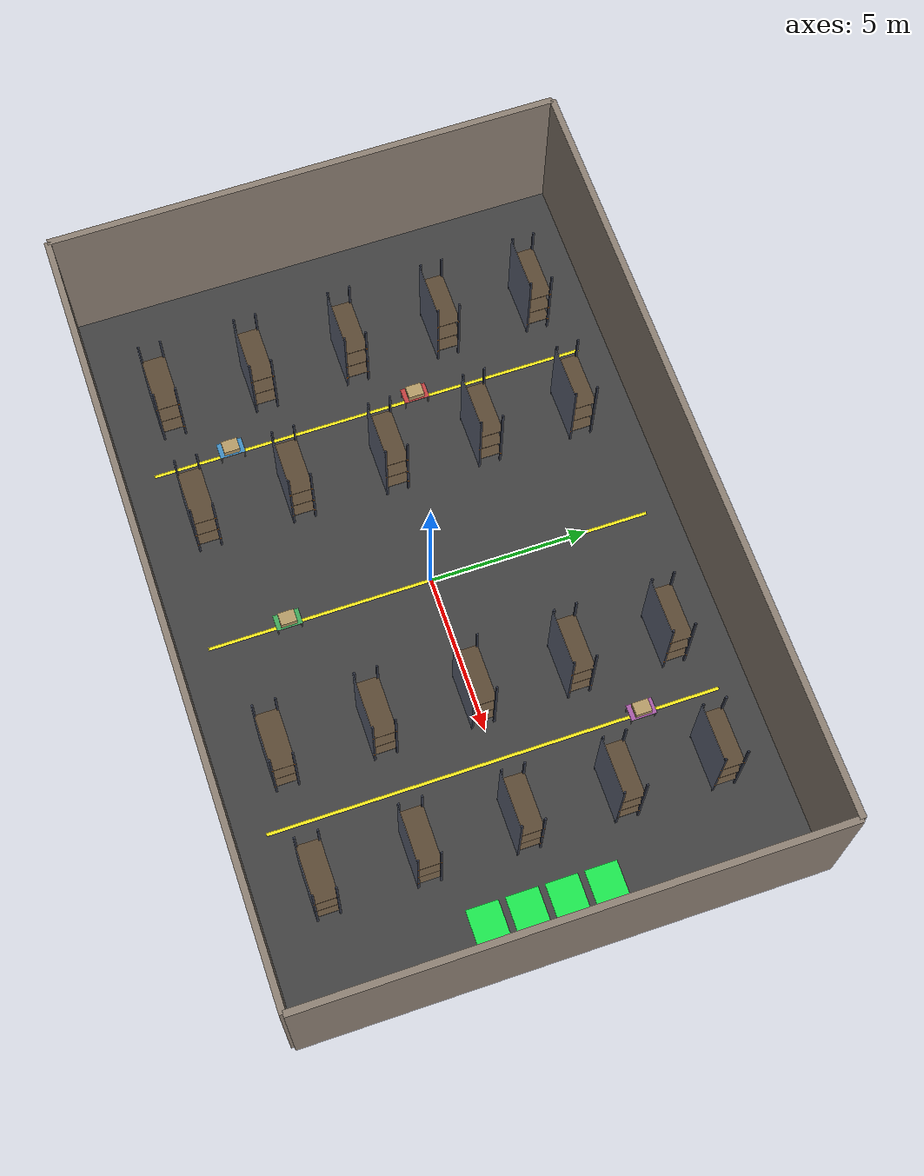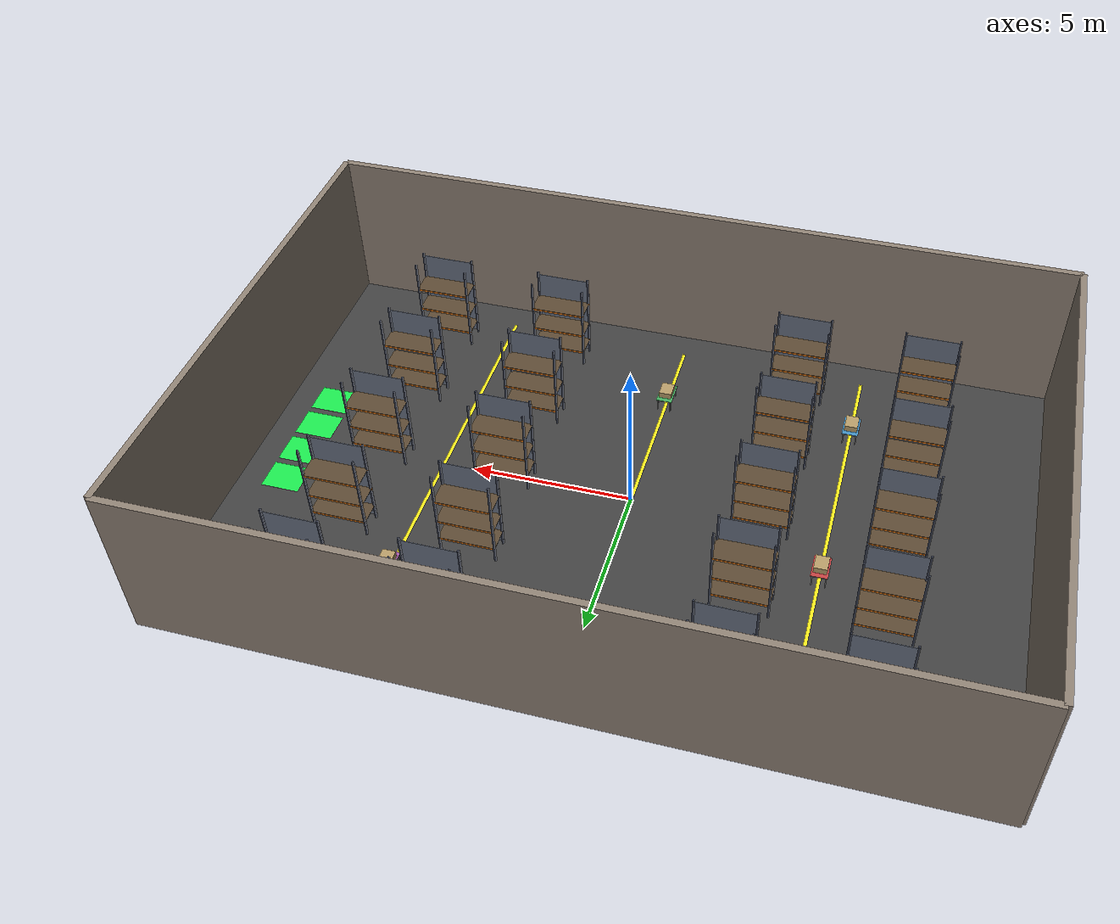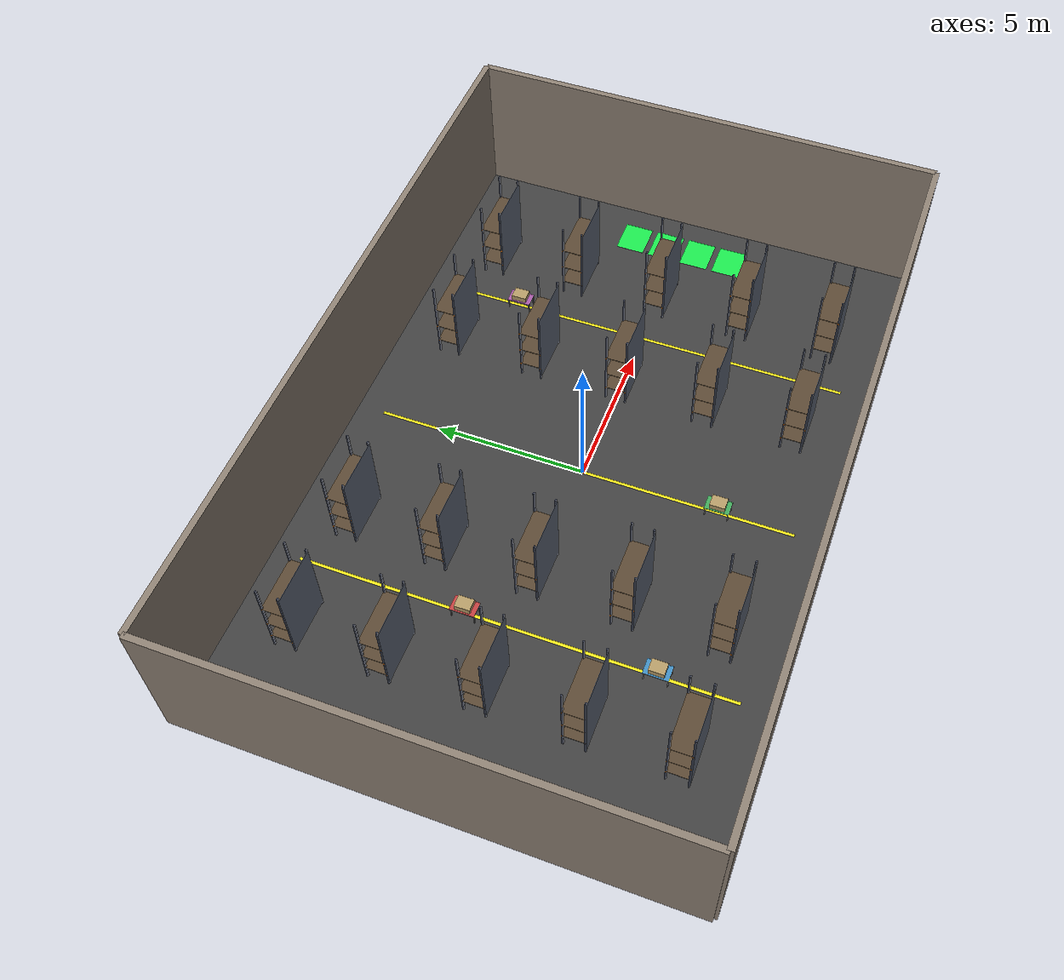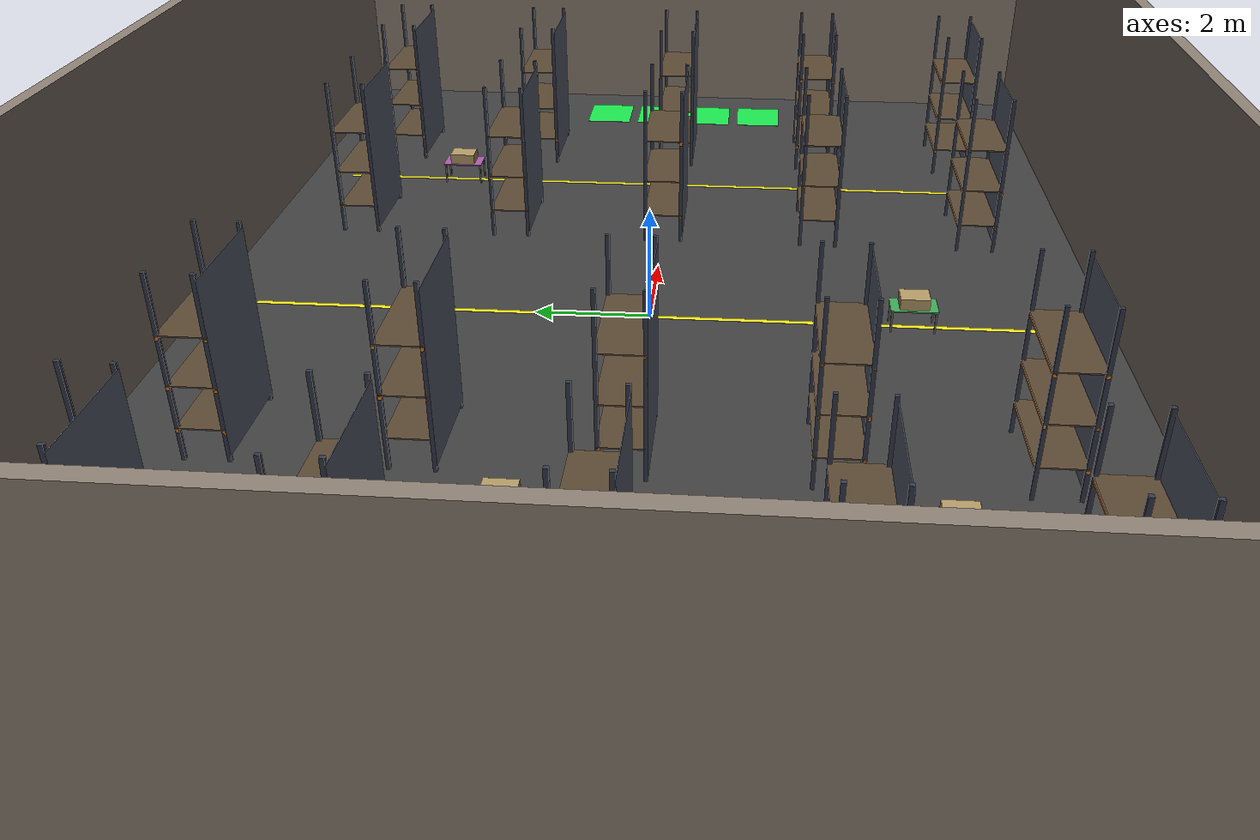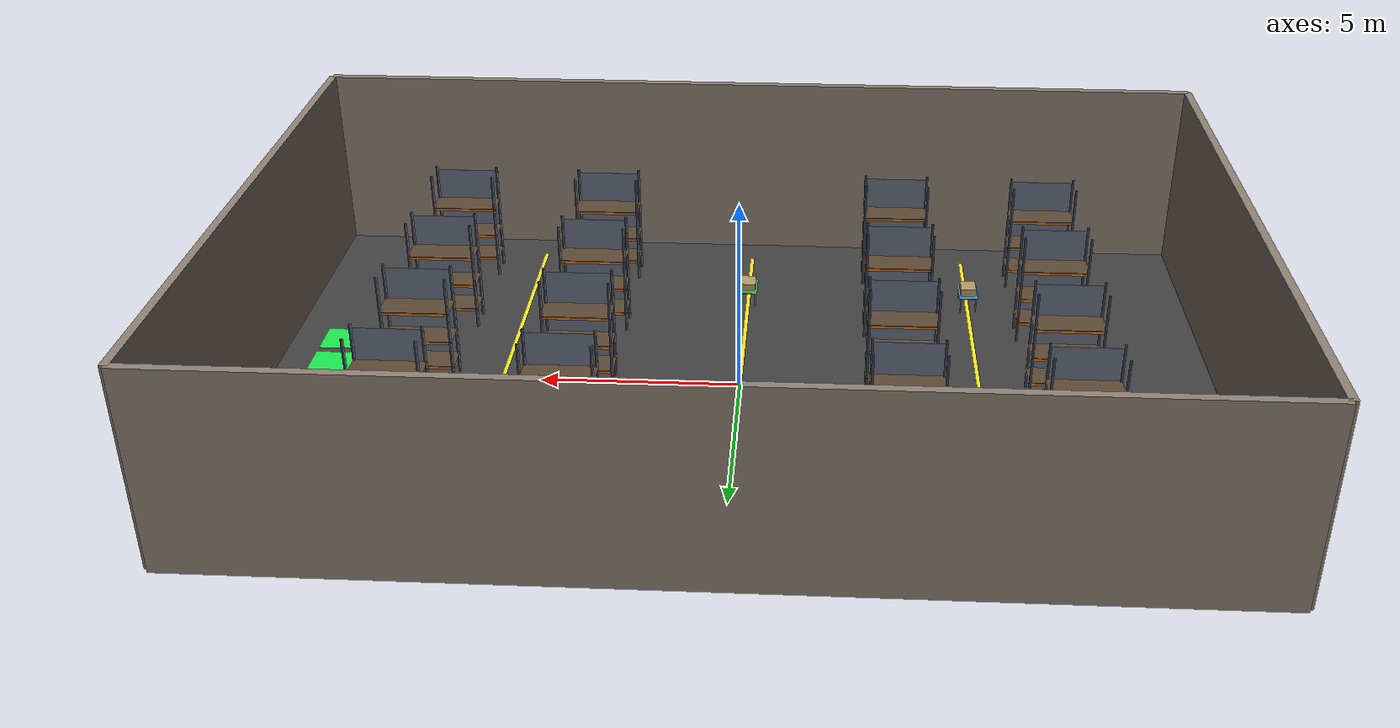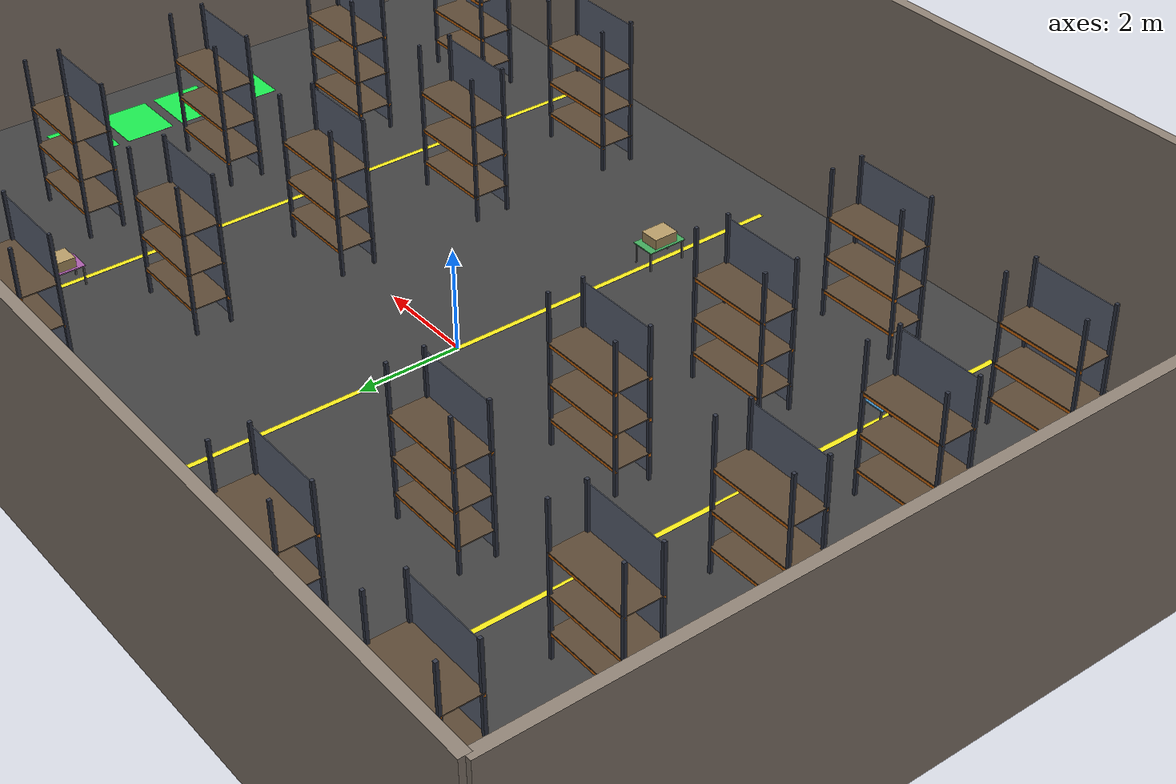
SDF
<?xml version="1.0"?>
<sdf version="1.8">
  <world name="warehouse_world">

    <physics name="physics" type="ignored">
      <max_step_size>0.001</max_step_size>
      <real_time_factor>1.0</real_time_factor>
    </physics>

    <plugin filename="ignition-gazebo-physics-system"
            name="ignition::gazebo::systems::Physics"/>
    <plugin filename="ignition-gazebo-user-commands-system"
            name="ignition::gazebo::systems::UserCommands"/>
    <plugin filename="ignition-gazebo-scene-broadcaster-system"
            name="ignition::gazebo::systems::SceneBroadcaster"/>
    <plugin filename="ignition-gazebo-sensors-system"
            name="ignition::gazebo::systems::Sensors">
      <render_engine>ogre2</render_engine>
    </plugin>
    <plugin filename="ignition-gazebo-contact-system"
            name="ignition::gazebo::systems::Contact"/>

    <!-- ========================================================
         SCENE & LIGHTING — Industrial Warehouse Ambiance
    ======================================================== -->
    <scene>
      <ambient>0.4 0.4 0.4 1.0</ambient>
      <background>0.15 0.15 0.2 1.0</background>
      <shadows>true</shadows>
    </scene>

    <!-- Sun (exterior daylight through roof) -->
    <light type="directional" name="sun">
      <pose>0 0 25 0 0 0</pose>
      <cast_shadows>true</cast_shadows>
      <diffuse>0.85 0.85 0.8 1</diffuse>
      <specular>0.3 0.3 0.3 1</specular>
      <direction>-0.3 0.2 -0.9</direction>
    </light>

    <!-- Row of overhead warehouse lights -->
    <light type="point" name="warehouse_light_1">
      <pose>-8 -5 6 0 0 0</pose>
      <diffuse>0.9 0.87 0.75 1</diffuse>
      <specular>0.2 0.2 0.15 1</specular>
      <attenuation><range>30</range><constant>0.3</constant><linear>0.01</linear><quadratic>0.001</quadratic></attenuation>
      <cast_shadows>false</cast_shadows>
    </light>
    <light type="point" name="warehouse_light_2">
      <pose>0 -5 6 0 0 0</pose>
      <diffuse>0.9 0.87 0.75 1</diffuse>
      <specular>0.2 0.2 0.15 1</specular>
      <attenuation><range>30</range><constant>0.3</constant><linear>0.01</linear><quadratic>0.001</quadratic></attenuation>
      <cast_shadows>false</cast_shadows>
    </light>
    <light type="point" name="warehouse_light_3">
      <pose>8 -5 6 0 0 0</pose>
      <diffuse>0.9 0.87 0.75 1</diffuse>
      <specular>0.2 0.2 0.15 1</specular>
      <attenuation><range>30</range><constant>0.3</constant><linear>0.01</linear><quadratic>0.001</quadratic></attenuation>
      <cast_shadows>false</cast_shadows>
    </light>
    <light type="point" name="warehouse_light_4">
      <pose>-8 5 6 0 0 0</pose>
      <diffuse>0.9 0.87 0.75 1</diffuse>
      <specular>0.2 0.2 0.15 1</specular>
      <attenuation><range>30</range><constant>0.3</constant><linear>0.01</linear><quadratic>0.001</quadratic></attenuation>
      <cast_shadows>false</cast_shadows>
    </light>
    <light type="point" name="warehouse_light_5">
      <pose>0 5 6 0 0 0</pose>
      <diffuse>0.9 0.87 0.75 1</diffuse>
      <specular>0.2 0.2 0.15 1</specular>
      <attenuation><range>30</range><constant>0.3</constant><linear>0.01</linear><quadratic>0.001</quadratic></attenuation>
      <cast_shadows>false</cast_shadows>
    </light>
    <light type="point" name="warehouse_light_6">
      <pose>8 5 6 0 0 0</pose>
      <diffuse>0.9 0.87 0.75 1</diffuse>
      <specular>0.2 0.2 0.15 1</specular>
      <attenuation><range>30</range><constant>0.3</constant><linear>0.01</linear><quadratic>0.001</quadratic></attenuation>
      <cast_shadows>false</cast_shadows>
    </light>

    <!-- FLOOR — polished concrete -->
    <model name="floor">
      <static>true</static>
      <pose>0 0 -0.01 0 0 0</pose>
      <link name="link">
        <collision name="col"><geometry><box><size>24 16 0.02</size></box></geometry></collision>
        <visual name="vis">
          <geometry><box><size>24 16 0.02</size></box></geometry>
          <material>
            <ambient>0.2 0.2 0.2 1</ambient>
            <diffuse>0.25 0.25 0.25 1</diffuse>
          </material>
        </visual>
      </link>
    </model>

    <!-- WALLS -->
    <model name="wall_north">
      <static>true</static><pose>0 8 2.5 0 0 0</pose>
      <link name="link">
        <collision name="col"><geometry><box><size>24 0.2 5</size></box></geometry></collision>
        <visual name="vis"><geometry><box><size>24 0.2 5</size></box></geometry>
          <material><ambient>0.5 0.45 0.4 1</ambient><diffuse>0.55 0.5 0.45 1</diffuse></material></visual>
      </link>
    </model>
    <model name="wall_south">
      <static>true</static><pose>0 -8 2.5 0 0 0</pose>
      <link name="link">
        <collision name="col"><geometry><box><size>24 0.2 5</size></box></geometry></collision>
        <visual name="vis"><geometry><box><size>24 0.2 5</size></box></geometry>
          <material><ambient>0.5 0.45 0.4 1</ambient><diffuse>0.55 0.5 0.45 1</diffuse></material></visual>
      </link>
    </model>
    <model name="wall_east">
      <static>true</static><pose>12 0 2.5 0 0 0</pose>
      <link name="link">
        <collision name="col"><geometry><box><size>0.2 16 5</size></box></geometry></collision>
        <visual name="vis"><geometry><box><size>0.2 16 5</size></box></geometry>
          <material><ambient>0.5 0.45 0.4 1</ambient><diffuse>0.55 0.5 0.45 1</diffuse></material></visual>
      </link>
    </model>
    <model name="wall_west">
      <static>true</static><pose>-12 0 2.5 0 0 0</pose>
      <link name="link">
        <collision name="col"><geometry><box><size>0.2 16 5</size></box></geometry></collision>
        <visual name="vis"><geometry><box><size>0.2 16 5</size></box></geometry>
          <material><ambient>0.5 0.45 0.4 1</ambient><diffuse>0.55 0.5 0.45 1</diffuse></material></visual>
      </link>
    </model>

    <!-- ===== ROW A (x = -8): 5 racks along y ===== -->

    <model name="rack_A1">
      <static>true</static><pose>-8 -6 0 0 0 0</pose>
      <link name="link">
        <!-- 4 Uprights (steel blue-grey) -->
        <visual name="u1"><pose>0.84 0.34 1.5 0 0 0</pose><geometry><box><size>0.06 0.06 3.0</size></box></geometry><material><ambient>0.15 0.18 0.22 1</ambient><diffuse>0.20 0.22 0.28 1</diffuse></material></visual>
        <collision name="u1c"><pose>0.84 0.34 1.5 0 0 0</pose><geometry><box><size>0.06 0.06 3.0</size></box></geometry></collision>
        <visual name="u2"><pose>0.84 -0.34 1.5 0 0 0</pose><geometry><box><size>0.06 0.06 3.0</size></box></geometry><material><ambient>0.15 0.18 0.22 1</ambient><diffuse>0.20 0.22 0.28 1</diffuse></material></visual>
        <collision name="u2c"><pose>0.84 -0.34 1.5 0 0 0</pose><geometry><box><size>0.06 0.06 3.0</size></box></geometry></collision>
        <visual name="u3"><pose>-0.84 0.34 1.5 0 0 0</pose><geometry><box><size>0.06 0.06 3.0</size></box></geometry><material><ambient>0.15 0.18 0.22 1</ambient><diffuse>0.20 0.22 0.28 1</diffuse></material></visual>
        <collision name="u3c"><pose>-0.84 0.34 1.5 0 0 0</pose><geometry><box><size>0.06 0.06 3.0</size></box></geometry></collision>
        <visual name="u4"><pose>-0.84 -0.34 1.5 0 0 0</pose><geometry><box><size>0.06 0.06 3.0</size></box></geometry><material><ambient>0.15 0.18 0.22 1</ambient><diffuse>0.20 0.22 0.28 1</diffuse></material></visual>
        <collision name="u4c"><pose>-0.84 -0.34 1.5 0 0 0</pose><geometry><box><size>0.06 0.06 3.0</size></box></geometry></collision>
        <!-- Beam Level 1 — z=0.50 (orange) -->
        <visual name="b1f"><pose>0 0.34 0.50 0 0 0</pose><geometry><box><size>1.74 0.05 0.06</size></box></geometry><material><ambient>0.90 0.45 0.05 1</ambient><diffuse>0.92 0.48 0.08 1</diffuse></material></visual>
        <collision name="b1fc"><pose>0 0.34 0.50 0 0 0</pose><geometry><box><size>1.74 0.05 0.06</size></box></geometry></collision>
        <visual name="b1b"><pose>0 -0.34 0.50 0 0 0</pose><geometry><box><size>1.74 0.05 0.06</size></box></geometry><material><ambient>0.90 0.45 0.05 1</ambient><diffuse>0.92 0.48 0.08 1</diffuse></material></visual>
        <collision name="b1bc"><pose>0 -0.34 0.50 0 0 0</pose><geometry><box><size>1.74 0.05 0.06</size></box></geometry></collision>
        <!-- Shelf deck 1 (plywood) -->
        <visual name="d1"><pose>0 0 0.54 0 0 0</pose><geometry><box><size>1.74 0.74 0.02</size></box></geometry><material><ambient>0.30 0.25 0.18 1</ambient><diffuse>0.35 0.28 0.20 1</diffuse></material></visual>
        <collision name="d1c"><pose>0 0 0.54 0 0 0</pose><geometry><box><size>1.74 0.74 0.02</size></box></geometry></collision>
        <!-- Beam Level 2 — z=1.20 -->
        <visual name="b2f"><pose>0 0.34 1.20 0 0 0</pose><geometry><box><size>1.74 0.05 0.06</size></box></geometry><material><ambient>0.90 0.45 0.05 1</ambient><diffuse>0.92 0.48 0.08 1</diffuse></material></visual>
        <collision name="b2fc"><pose>0 0.34 1.20 0 0 0</pose><geometry><box><size>1.74 0.05 0.06</size></box></geometry></collision>
        <visual name="b2b"><pose>0 -0.34 1.20 0 0 0</pose><geometry><box><size>1.74 0.05 0.06</size></box></geometry><material><ambient>0.90 0.45 0.05 1</ambient><diffuse>0.92 0.48 0.08 1</diffuse></material></visual>
        <collision name="b2bc"><pose>0 -0.34 1.20 0 0 0</pose><geometry><box><size>1.74 0.05 0.06</size></box></geometry></collision>
        <!-- Shelf deck 2 -->
        <visual name="d2"><pose>0 0 1.24 0 0 0</pose><geometry><box><size>1.74 0.74 0.02</size></box></geometry><material><ambient>0.30 0.25 0.18 1</ambient><diffuse>0.35 0.28 0.20 1</diffuse></material></visual>
        <collision name="d2c"><pose>0 0 1.24 0 0 0</pose><geometry><box><size>1.74 0.74 0.02</size></box></geometry></collision>
        <!-- Beam Level 3 — z=2.00 -->
        <visual name="b3f"><pose>0 0.34 2.00 0 0 0</pose><geometry><box><size>1.74 0.05 0.06</size></box></geometry><material><ambient>0.90 0.45 0.05 1</ambient><diffuse>0.92 0.48 0.08 1</diffuse></material></visual>
        <collision name="b3fc"><pose>0 0.34 2.00 0 0 0</pose><geometry><box><size>1.74 0.05 0.06</size></box></geometry></collision>
        <visual name="b3b"><pose>0 -0.34 2.00 0 0 0</pose><geometry><box><size>1.74 0.05 0.06</size></box></geometry><material><ambient>0.90 0.45 0.05 1</ambient><diffuse>0.92 0.48 0.08 1</diffuse></material></visual>
        <collision name="b3bc"><pose>0 -0.34 2.00 0 0 0</pose><geometry><box><size>1.74 0.05 0.06</size></box></geometry></collision>
        <!-- Shelf deck 3 -->
        <visual name="d3"><pose>0 0 2.04 0 0 0</pose><geometry><box><size>1.74 0.74 0.02</size></box></geometry><material><ambient>0.30 0.25 0.18 1</ambient><diffuse>0.35 0.28 0.20 1</diffuse></material></visual>
        <collision name="d3c"><pose>0 0 2.04 0 0 0</pose><geometry><box><size>1.74 0.74 0.02</size></box></geometry></collision>
        <!-- Back brace (X-pattern approximation) -->
        <visual name="brace"><pose>0 -0.37 1.5 0 0 0</pose><geometry><box><size>1.74 0.01 2.8</size></box></geometry><material><ambient>0.35 0.38 0.45 1</ambient><diffuse>0.40 0.43 0.50 1</diffuse></material></visual>
      </link>
    </model>

    <model name="rack_A2">
      <static>true</static><pose>-8 -3 0 0 0 0</pose>
      <link name="link">
        <visual name="u1"><pose>0.84 0.34 1.5 0 0 0</pose><geometry><box><size>0.06 0.06 3.0</size></box></geometry><material><ambient>0.15 0.18 0.22 1</ambient><diffuse>0.20 0.22 0.28 1</diffuse></material></visual>
        <collision name="u1c"><pose>0.84 0.34 1.5 0 0 0</pose><geometry><box><size>0.06 0.06 3.0</size></box></geometry></collision>
        <visual name="u2"><pose>0.84 -0.34 1.5 0 0 0</pose><geometry><box><size>0.06 0.06 3.0</size></box></geometry><material><ambient>0.15 0.18 0.22 1</ambient><diffuse>0.20 0.22 0.28 1</diffuse></material></visual>
        <collision name="u2c"><pose>0.84 -0.34 1.5 0 0 0</pose><geometry><box><size>0.06 0.06 3.0</size></box></geometry></collision>
        <visual name="u3"><pose>-0.84 0.34 1.5 0 0 0</pose><geometry><box><size>0.06 0.06 3.0</size></box></geometry><material><ambient>0.15 0.18 0.22 1</ambient><diffuse>0.20 0.22 0.28 1</diffuse></material></visual>
        <collision name="u3c"><pose>-0.84 0.34 1.5 0 0 0</pose><geometry><box><size>0.06 0.06 3.0</size></box></geometry></collision>
        <visual name="u4"><pose>-0.84 -0.34 1.5 0 0 0</pose><geometry><box><size>0.06 0.06 3.0</size></box></geometry><material><ambient>0.15 0.18 0.22 1</ambient><diffuse>0.20 0.22 0.28 1</diffuse></material></visual>
        <collision name="u4c"><pose>-0.84 -0.34 1.5 0 0 0</pose><geometry><box><size>0.06 0.06 3.0</size></box></geometry></collision>
        <visual name="b1f"><pose>0 0.34 0.50 0 0 0</pose><geometry><box><size>1.74 0.05 0.06</size></box></geometry><material><ambient>0.90 0.45 0.05 1</ambient><diffuse>0.92 0.48 0.08 1</diffuse></material></visual>
        <collision name="b1fc"><pose>0 0.34 0.50 0 0 0</pose><geometry><box><size>1.74 0.05 0.06</size></box></geometry></collision>
        <visual name="b1b"><pose>0 -0.34 0.50 0 0 0</pose><geometry><box><size>1.74 0.05 0.06</size></box></geometry><material><ambient>0.90 0.45 0.05 1</ambient><diffuse>0.92 0.48 0.08 1</diffuse></material></visual>
        <collision name="b1bc"><pose>0 -0.34 0.50 0 0 0</pose><geometry><box><size>1.74 0.05 0.06</size></box></geometry></collision>
        <visual name="d1"><pose>0 0 0.54 0 0 0</pose><geometry><box><size>1.74 0.74 0.02</size></box></geometry><material><ambient>0.30 0.25 0.18 1</ambient><diffuse>0.35 0.28 0.20 1</diffuse></material></visual>
        <collision name="d1c"><pose>0 0 0.54 0 0 0</pose><geometry><box><size>1.74 0.74 0.02</size></box></geometry></collision>
        <visual name="b2f"><pose>0 0.34 1.20 0 0 0</pose><geometry><box><size>1.74 0.05 0.06</size></box></geometry><material><ambient>0.90 0.45 0.05 1</ambient><diffuse>0.92 0.48 0.08 1</diffuse></material></visual>
        <collision name="b2fc"><pose>0 0.34 1.20 0 0 0</pose><geometry><box><size>1.74 0.05 0.06</size></box></geometry></collision>
        <visual name="b2b"><pose>0 -0.34 1.20 0 0 0</pose><geometry><box><size>1.74 0.05 0.06</size></box></geometry><material><ambient>0.90 0.45 0.05 1</ambient><diffuse>0.92 0.48 0.08 1</diffuse></material></visual>
        <collision name="b2bc"><pose>0 -0.34 1.20 0 0 0</pose><geometry><box><size>1.74 0.05 0.06</size></box></geometry></collision>
        <visual name="d2"><pose>0 0 1.24 0 0 0</pose><geometry><box><size>1.74 0.74 0.02</size></box></geometry><material><ambient>0.30 0.25 0.18 1</ambient><diffuse>0.35 0.28 0.20 1</diffuse></material></visual>
        <collision name="d2c"><pose>0 0 1.24 0 0 0</pose><geometry><box><size>1.74 0.74 0.02</size></box></geometry></collision>
        <visual name="b3f"><pose>0 0.34 2.00 0 0 0</pose><geometry><box><size>1.74 0.05 0.06</size></box></geometry><material><ambient>0.90 0.45 0.05 1</ambient><diffuse>0.92 0.48 0.08 1</diffuse></material></visual>
        <collision name="b3fc"><pose>0 0.34 2.00 0 0 0</pose><geometry><box><size>1.74 0.05 0.06</size></box></geometry></collision>
        <visual name="b3b"><pose>0 -0.34 2.00 0 0 0</pose><geometry><box><size>1.74 0.05 0.06</size></box></geometry><material><ambient>0.90 0.45 0.05 1</ambient><diffuse>0.92 0.48 0.08 1</diffuse></material></visual>
        <collision name="b3bc"><pose>0 -0.34 2.00 0 0 0</pose><geometry><box><size>1.74 0.05 0.06</size></box></geometry></collision>
        <visual name="d3"><pose>0 0 2.04 0 0 0</pose><geometry><box><size>1.74 0.74 0.02</size></box></geometry><material><ambient>0.30 0.25 0.18 1</ambient><diffuse>0.35 0.28 0.20 1</diffuse></material></visual>
        <collision name="d3c"><pose>0 0 2.04 0 0 0</pose><geometry><box><size>1.74 0.74 0.02</size></box></geometry></collision>
        <visual name="brace"><pose>0 -0.37 1.5 0 0 0</pose><geometry><box><size>1.74 0.01 2.8</size></box></geometry><material><ambient>0.35 0.38 0.45 1</ambient><diffuse>0.40 0.43 0.50 1</diffuse></material></visual>
      </link>
    </model>

    <model name="rack_A3">
      <static>true</static><pose>-8 0 0 0 0 0</pose>
      <link name="link">
        <visual name="u1"><pose>0.84 0.34 1.5 0 0 0</pose><geometry><box><size>0.06 0.06 3.0</size></box></geometry><material><ambient>0.15 0.18 0.22 1</ambient><diffuse>0.20 0.22 0.28 1</diffuse></material></visual>
        <collision name="u1c"><pose>0.84 0.34 1.5 0 0 0</pose><geometry><box><size>0.06 0.06 3.0</size></box></geometry></collision>
        <visual name="u2"><pose>0.84 -0.34 1.5 0 0 0</pose><geometry><box><size>0.06 0.06 3.0</size></box></geometry><material><ambient>0.15 0.18 0.22 1</ambient><diffuse>0.20 0.22 0.28 1</diffuse></material></visual>
        <collision name="u2c"><pose>0.84 -0.34 1.5 0 0 0</pose><geometry><box><size>0.06 0.06 3.0</size></box></geometry></collision>
        <visual name="u3"><pose>-0.84 0.34 1.5 0 0 0</pose><geometry><box><size>0.06 0.06 3.0</size></box></geometry><material><ambient>0.15 0.18 0.22 1</ambient><diffuse>0.20 0.22 0.28 1</diffuse></material></visual>
        <collision name="u3c"><pose>-0.84 0.34 1.5 0 0 0</pose><geometry><box><size>0.06 0.06 3.0</size></box></geometry></collision>
        <visual name="u4"><pose>-0.84 -0.34 1.5 0 0 0</pose><geometry><box><size>0.06 0.06 3.0</size></box></geometry><material><ambient>0.15 0.18 0.22 1</ambient><diffuse>0.20 0.22 0.28 1</diffuse></material></visual>
        <collision name="u4c"><pose>-0.84 -0.34 1.5 0 0 0</pose><geometry><box><size>0.06 0.06 3.0</size></box></geometry></collision>
        <visual name="b1f"><pose>0 0.34 0.50 0 0 0</pose><geometry><box><size>1.74 0.05 0.06</size></box></geometry><material><ambient>0.90 0.45 0.05 1</ambient><diffuse>0.92 0.48 0.08 1</diffuse></material></visual>
        <collision name="b1fc"><pose>0 0.34 0.50 0 0 0</pose><geometry><box><size>1.74 0.05 0.06</size></box></geometry></collision>
        <visual name="b1b"><pose>0 -0.34 0.50 0 0 0</pose><geometry><box><size>1.74 0.05 0.06</size></box></geometry><material><ambient>0.90 0.45 0.05 1</ambient><diffuse>0.92 0.48 0.08 1</diffuse></material></visual>
        <collision name="b1bc"><pose>0 -0.34 0.50 0 0 0</pose><geometry><box><size>1.74 0.05 0.06</size></box></geometry></collision>
        <visual name="d1"><pose>0 0 0.54 0 0 0</pose><geometry><box><size>1.74 0.74 0.02</size></box></geometry><material><ambient>0.30 0.25 0.18 1</ambient><diffuse>0.35 0.28 0.20 1</diffuse></material></visual>
        <collision name="d1c"><pose>0 0 0.54 0 0 0</pose><geometry><box><size>1.74 0.74 0.02</size></box></geometry></collision>
        <visual name="b2f"><pose>0 0.34 1.20 0 0 0</pose><geometry><box><size>1.74 0.05 0.06</size></box></geometry><material><ambient>0.90 0.45 0.05 1</ambient><diffuse>0.92 0.48 0.08 1</diffuse></material></visual>
        <collision name="b2fc"><pose>0 0.34 1.20 0 0 0</pose><geometry><box><size>1.74 0.05 0.06</size></box></geometry></collision>
        <visual name="b2b"><pose>0 -0.34 1.20 0 0 0</pose><geometry><box><size>1.74 0.05 0.06</size></box></geometry><material><ambient>0.90 0.45 0.05 1</ambient><diffuse>0.92 0.48 0.08 1</diffuse></material></visual>
        <collision name="b2bc"><pose>0 -0.34 1.20 0 0 0</pose><geometry><box><size>1.74 0.05 0.06</size></box></geometry></collision>
        <visual name="d2"><pose>0 0 1.24 0 0 0</pose><geometry><box><size>1.74 0.74 0.02</size></box></geometry><material><ambient>0.30 0.25 0.18 1</ambient><diffuse>0.35 0.28 0.20 1</diffuse></material></visual>
        <collision name="d2c"><pose>0 0 1.24 0 0 0</pose><geometry><box><size>1.74 0.74 0.02</size></box></geometry></collision>
        <visual name="b3f"><pose>0 0.34 2.00 0 0 0</pose><geometry><box><size>1.74 0.05 0.06</size></box></geometry><material><ambient>0.90 0.45 0.05 1</ambient><diffuse>0.92 0.48 0.08 1</diffuse></material></visual>
        <collision name="b3fc"><pose>0 0.34 2.00 0 0 0</pose><geometry><box><size>1.74 0.05 0.06</size></box></geometry></collision>
        <visual name="b3b"><pose>0 -0.34 2.00 0 0 0</pose><geometry><box><size>1.74 0.05 0.06</size></box></geometry><material><ambient>0.90 0.45 0.05 1</ambient><diffuse>0.92 0.48 0.08 1</diffuse></material></visual>
        <collision name="b3bc"><pose>0 -0.34 2.00 0 0 0</pose><geometry><box><size>1.74 0.05 0.06</size></box></geometry></collision>
        <visual name="d3"><pose>0 0 2.04 0 0 0</pose><geometry><box><size>1.74 0.74 0.02</size></box></geometry><material><ambient>0.30 0.25 0.18 1</ambient><diffuse>0.35 0.28 0.20 1</diffuse></material></visual>
        <collision name="d3c"><pose>0 0 2.04 0 0 0</pose><geometry><box><size>1.74 0.74 0.02</size></box></geometry></collision>
        <visual name="brace"><pose>0 -0.37 1.5 0 0 0</pose><geometry><box><size>1.74 0.01 2.8</size></box></geometry><material><ambient>0.35 0.38 0.45 1</ambient><diffuse>0.40 0.43 0.50 1</diffuse></material></visual>
      </link>
    </model>

    <model name="rack_A4">
      <static>true</static><pose>-8 3 0 0 0 0</pose>
      <link name="link">
        <visual name="u1"><pose>0.84 0.34 1.5 0 0 0</pose><geometry><box><size>0.06 0.06 3.0</size></box></geometry><material><ambient>0.15 0.18 0.22 1</ambient><diffuse>0.20 0.22 0.28 1</diffuse></material></visual><collision name="u1c"><pose>0.84 0.34 1.5 0 0 0</pose><geometry><box><size>0.06 0.06 3.0</size></box></geometry></collision>
        <visual name="u2"><pose>0.84 -0.34 1.5 0 0 0</pose><geometry><box><size>0.06 0.06 3.0</size></box></geometry><material><ambient>0.15 0.18 0.22 1</ambient><diffuse>0.20 0.22 0.28 1</diffuse></material></visual><collision name="u2c"><pose>0.84 -0.34 1.5 0 0 0</pose><geometry><box><size>0.06 0.06 3.0</size></box></geometry></collision>
        <visual name="u3"><pose>-0.84 0.34 1.5 0 0 0</pose><geometry><box><size>0.06 0.06 3.0</size></box></geometry><material><ambient>0.15 0.18 0.22 1</ambient><diffuse>0.20 0.22 0.28 1</diffuse></material></visual><collision name="u3c"><pose>-0.84 0.34 1.5 0 0 0</pose><geometry><box><size>0.06 0.06 3.0</size></box></geometry></collision>
        <visual name="u4"><pose>-0.84 -0.34 1.5 0 0 0</pose><geometry><box><size>0.06 0.06 3.0</size></box></geometry><material><ambient>0.15 0.18 0.22 1</ambient><diffuse>0.20 0.22 0.28 1</diffuse></material></visual><collision name="u4c"><pose>-0.84 -0.34 1.5 0 0 0</pose><geometry><box><size>0.06 0.06 3.0</size></box></geometry></collision>
        <visual name="b1f"><pose>0 0.34 0.50 0 0 0</pose><geometry><box><size>1.74 0.05 0.06</size></box></geometry><material><ambient>0.90 0.45 0.05 1</ambient><diffuse>0.92 0.48 0.08 1</diffuse></material></visual><collision name="b1fc"><pose>0 0.34 0.50 0 0 0</pose><geometry><box><size>1.74 0.05 0.06</size></box></geometry></collision>
        <visual name="b1b"><pose>0 -0.34 0.50 0 0 0</pose><geometry><box><size>1.74 0.05 0.06</size></box></geometry><material><ambient>0.90 0.45 0.05 1</ambient><diffuse>0.92 0.48 0.08 1</diffuse></material></visual><collision name="b1bc"><pose>0 -0.34 0.50 0 0 0</pose><geometry><box><size>1.74 0.05 0.06</size></box></geometry></collision>
        <visual name="d1"><pose>0 0 0.54 0 0 0</pose><geometry><box><size>1.74 0.74 0.02</size></box></geometry><material><ambient>0.30 0.25 0.18 1</ambient><diffuse>0.35 0.28 0.20 1</diffuse></material></visual><collision name="d1c"><pose>0 0 0.54 0 0 0</pose><geometry><box><size>1.74 0.74 0.02</size></box></geometry></collision>
        <visual name="b2f"><pose>0 0.34 1.20 0 0 0</pose><geometry><box><size>1.74 0.05 0.06</size></box></geometry><material><ambient>0.90 0.45 0.05 1</ambient><diffuse>0.92 0.48 0.08 1</diffuse></material></visual><collision name="b2fc"><pose>0 0.34 1.20 0 0 0</pose><geometry><box><size>1.74 0.05 0.06</size></box></geometry></collision>
        <visual name="b2b"><pose>0 -0.34 1.20 0 0 0</pose><geometry><box><size>1.74 0.05 0.06</size></box></geometry><material><ambient>0.90 0.45 0.05 1</ambient><diffuse>0.92 0.48 0.08 1</diffuse></material></visual><collision name="b2bc"><pose>0 -0.34 1.20 0 0 0</pose><geometry><box><size>1.74 0.05 0.06</size></box></geometry></collision>
        <visual name="d2"><pose>0 0 1.24 0 0 0</pose><geometry><box><size>1.74 0.74 0.02</size></box></geometry><material><ambient>0.30 0.25 0.18 1</ambient><diffuse>0.35 0.28 0.20 1</diffuse></material></visual><collision name="d2c"><pose>0 0 1.24 0 0 0</pose><geometry><box><size>1.74 0.74 0.02</size></box></geometry></collision>
        <visual name="b3f"><pose>0 0.34 2.00 0 0 0</pose><geometry><box><size>1.74 0.05 0.06</size></box></geometry><material><ambient>0.90 0.45 0.05 1</ambient><diffuse>0.92 0.48 0.08 1</diffuse></material></visual><collision name="b3fc"><pose>0 0.34 2.00 0 0 0</pose><geometry><box><size>1.74 0.05 0.06</size></box></geometry></collision>
        <visual name="b3b"><pose>0 -0.34 2.00 0 0 0</pose><geometry><box><size>1.74 0.05 0.06</size></box></geometry><material><ambient>0.90 0.45 0.05 1</ambient><diffuse>0.92 0.48 0.08 1</diffuse></material></visual><collision name="b3bc"><pose>0 -0.34 2.00 0 0 0</pose><geometry><box><size>1.74 0.05 0.06</size></box></geometry></collision>
        <visual name="d3"><pose>0 0 2.04 0 0 0</pose><geometry><box><size>1.74 0.74 0.02</size></box></geometry><material><ambient>0.30 0.25 0.18 1</ambient><diffuse>0.35 0.28 0.20 1</diffuse></material></visual><collision name="d3c"><pose>0 0 2.04 0 0 0</pose><geometry><box><size>1.74 0.74 0.02</size></box></geometry></collision>
        <visual name="brace"><pose>0 -0.37 1.5 0 0 0</pose><geometry><box><size>1.74 0.01 2.8</size></box></geometry><material><ambient>0.35 0.38 0.45 1</ambient><diffuse>0.40 0.43 0.50 1</diffuse></material></visual>
      </link>
    </model>

    <model name="rack_A5">
      <static>true</static><pose>-8 6 0 0 0 0</pose>
      <link name="link">
        <visual name="u1"><pose>0.84 0.34 1.5 0 0 0</pose><geometry><box><size>0.06 0.06 3.0</size></box></geometry><material><ambient>0.15 0.18 0.22 1</ambient><diffuse>0.20 0.22 0.28 1</diffuse></material></visual><collision name="u1c"><pose>0.84 0.34 1.5 0 0 0</pose><geometry><box><size>0.06 0.06 3.0</size></box></geometry></collision>
        <visual name="u2"><pose>0.84 -0.34 1.5 0 0 0</pose><geometry><box><size>0.06 0.06 3.0</size></box></geometry><material><ambient>0.15 0.18 0.22 1</ambient><diffuse>0.20 0.22 0.28 1</diffuse></material></visual><collision name="u2c"><pose>0.84 -0.34 1.5 0 0 0</pose><geometry><box><size>0.06 0.06 3.0</size></box></geometry></collision>
        <visual name="u3"><pose>-0.84 0.34 1.5 0 0 0</pose><geometry><box><size>0.06 0.06 3.0</size></box></geometry><material><ambient>0.15 0.18 0.22 1</ambient><diffuse>0.20 0.22 0.28 1</diffuse></material></visual><collision name="u3c"><pose>-0.84 0.34 1.5 0 0 0</pose><geometry><box><size>0.06 0.06 3.0</size></box></geometry></collision>
        <visual name="u4"><pose>-0.84 -0.34 1.5 0 0 0</pose><geometry><box><size>0.06 0.06 3.0</size></box></geometry><material><ambient>0.15 0.18 0.22 1</ambient><diffuse>0.20 0.22 0.28 1</diffuse></material></visual><collision name="u4c"><pose>-0.84 -0.34 1.5 0 0 0</pose><geometry><box><size>0.06 0.06 3.0</size></box></geometry></collision>
        <visual name="b1f"><pose>0 0.34 0.50 0 0 0</pose><geometry><box><size>1.74 0.05 0.06</size></box></geometry><material><ambient>0.90 0.45 0.05 1</ambient><diffuse>0.92 0.48 0.08 1</diffuse></material></visual><collision name="b1fc"><pose>0 0.34 0.50 0 0 0</pose><geometry><box><size>1.74 0.05 0.06</size></box></geometry></collision>
        <visual name="b1b"><pose>0 -0.34 0.50 0 0 0</pose><geometry><box><size>1.74 0.05 0.06</size></box></geometry><material><ambient>0.90 0.45 0.05 1</ambient><diffuse>0.92 0.48 0.08 1</diffuse></material></visual><collision name="b1bc"><pose>0 -0.34 0.50 0 0 0</pose><geometry><box><size>1.74 0.05 0.06</size></box></geometry></collision>
        <visual name="d1"><pose>0 0 0.54 0 0 0</pose><geometry><box><size>1.74 0.74 0.02</size></box></geometry><material><ambient>0.30 0.25 0.18 1</ambient><diffuse>0.35 0.28 0.20 1</diffuse></material></visual><collision name="d1c"><pose>0 0 0.54 0 0 0</pose><geometry><box><size>1.74 0.74 0.02</size></box></geometry></collision>
        <visual name="b2f"><pose>0 0.34 1.20 0 0 0</pose><geometry><box><size>1.74 0.05 0.06</size></box></geometry><material><ambient>0.90 0.45 0.05 1</ambient><diffuse>0.92 0.48 0.08 1</diffuse></material></visual><collision name="b2fc"><pose>0 0.34 1.20 0 0 0</pose><geometry><box><size>1.74 0.05 0.06</size></box></geometry></collision>
        <visual name="b2b"><pose>0 -0.34 1.20 0 0 0</pose><geometry><box><size>1.74 0.05 0.06</size></box></geometry><material><ambient>0.90 0.45 0.05 1</ambient><diffuse>0.92 0.48 0.08 1</diffuse></material></visual><collision name="b2bc"><pose>0 -0.34 1.20 0 0 0</pose><geometry><box><size>1.74 0.05 0.06</size></box></geometry></collision>
        <visual name="d2"><pose>0 0 1.24 0 0 0</pose><geometry><box><size>1.74 0.74 0.02</size></box></geometry><material><ambient>0.30 0.25 0.18 1</ambient><diffuse>0.35 0.28 0.20 1</diffuse></material></visual><collision name="d2c"><pose>0 0 1.24 0 0 0</pose><geometry><box><size>1.74 0.74 0.02</size></box></geometry></collision>
        <visual name="b3f"><pose>0 0.34 2.00 0 0 0</pose><geometry><box><size>1.74 0.05 0.06</size></box></geometry><material><ambient>0.90 0.45 0.05 1</ambient><diffuse>0.92 0.48 0.08 1</diffuse></material></visual><collision name="b3fc"><pose>0 0.34 2.00 0 0 0</pose><geometry><box><size>1.74 0.05 0.06</size></box></geometry></collision>
        <visual name="b3b"><pose>0 -0.34 2.00 0 0 0</pose><geometry><box><size>1.74 0.05 0.06</size></box></geometry><material><ambient>0.90 0.45 0.05 1</ambient><diffuse>0.92 0.48 0.08 1</diffuse></material></visual><collision name="b3bc"><pose>0 -0.34 2.00 0 0 0</pose><geometry><box><size>1.74 0.05 0.06</size></box></geometry></collision>
        <visual name="d3"><pose>0 0 2.04 0 0 0</pose><geometry><box><size>1.74 0.74 0.02</size></box></geometry><material><ambient>0.30 0.25 0.18 1</ambient><diffuse>0.35 0.28 0.20 1</diffuse></material></visual><collision name="d3c"><pose>0 0 2.04 0 0 0</pose><geometry><box><size>1.74 0.74 0.02</size></box></geometry></collision>
        <visual name="brace"><pose>0 -0.37 1.5 0 0 0</pose><geometry><box><size>1.74 0.01 2.8</size></box></geometry><material><ambient>0.35 0.38 0.45 1</ambient><diffuse>0.40 0.43 0.50 1</diffuse></material></visual>
      </link>
    </model>

    <!-- ===== ROW B (x = -4): 5 racks ===== -->
    <model name="rack_B1"><static>true</static><pose>-4 -6 0 0 0 0</pose><link name="link">
      <visual name="u1"><pose>0.84 0.34 1.5 0 0 0</pose><geometry><box><size>0.06 0.06 3.0</size></box></geometry><material><ambient>0.15 0.18 0.22 1</ambient><diffuse>0.20 0.22 0.28 1</diffuse></material></visual><collision name="u1c"><pose>0.84 0.34 1.5 0 0 0</pose><geometry><box><size>0.06 0.06 3.0</size></box></geometry></collision>
      <visual name="u2"><pose>0.84 -0.34 1.5 0 0 0</pose><geometry><box><size>0.06 0.06 3.0</size></box></geometry><material><ambient>0.15 0.18 0.22 1</ambient><diffuse>0.20 0.22 0.28 1</diffuse></material></visual><collision name="u2c"><pose>0.84 -0.34 1.5 0 0 0</pose><geometry><box><size>0.06 0.06 3.0</size></box></geometry></collision>
      <visual name="u3"><pose>-0.84 0.34 1.5 0 0 0</pose><geometry><box><size>0.06 0.06 3.0</size></box></geometry><material><ambient>0.15 0.18 0.22 1</ambient><diffuse>0.20 0.22 0.28 1</diffuse></material></visual><collision name="u3c"><pose>-0.84 0.34 1.5 0 0 0</pose><geometry><box><size>0.06 0.06 3.0</size></box></geometry></collision>
      <visual name="u4"><pose>-0.84 -0.34 1.5 0 0 0</pose><geometry><box><size>0.06 0.06 3.0</size></box></geometry><material><ambient>0.15 0.18 0.22 1</ambient><diffuse>0.20 0.22 0.28 1</diffuse></material></visual><collision name="u4c"><pose>-0.84 -0.34 1.5 0 0 0</pose><geometry><box><size>0.06 0.06 3.0</size></box></geometry></collision>
      <visual name="b1f"><pose>0 0.34 0.50 0 0 0</pose><geometry><box><size>1.74 0.05 0.06</size></box></geometry><material><ambient>0.90 0.45 0.05 1</ambient><diffuse>0.92 0.48 0.08 1</diffuse></material></visual><collision name="b1fc"><pose>0 0.34 0.50 0 0 0</pose><geometry><box><size>1.74 0.05 0.06</size></box></geometry></collision>
      <visual name="b1b"><pose>0 -0.34 0.50 0 0 0</pose><geometry><box><size>1.74 0.05 0.06</size></box></geometry><material><ambient>0.90 0.45 0.05 1</ambient><diffuse>0.92 0.48 0.08 1</diffuse></material></visual><collision name="b1bc"><pose>0 -0.34 0.50 0 0 0</pose><geometry><box><size>1.74 0.05 0.06</size></box></geometry></collision>
      <visual name="d1"><pose>0 0 0.54 0 0 0</pose><geometry><box><size>1.74 0.74 0.02</size></box></geometry><material><ambient>0.30 0.25 0.18 1</ambient><diffuse>0.35 0.28 0.20 1</diffuse></material></visual><collision name="d1c"><pose>0 0 0.54 0 0 0</pose><geometry><box><size>1.74 0.74 0.02</size></box></geometry></collision>
      <visual name="b2f"><pose>0 0.34 1.20 0 0 0</pose><geometry><box><size>1.74 0.05 0.06</size></box></geometry><material><ambient>0.90 0.45 0.05 1</ambient><diffuse>0.92 0.48 0.08 1</diffuse></material></visual><collision name="b2fc"><pose>0 0.34 1.20 0 0 0</pose><geometry><box><size>1.74 0.05 0.06</size></box></geometry></collision>
      <visual name="b2b"><pose>0 -0.34 1.20 0 0 0</pose><geometry><box><size>1.74 0.05 0.06</size></box></geometry><material><ambient>0.90 0.45 0.05 1</ambient><diffuse>0.92 0.48 0.08 1</diffuse></material></visual><collision name="b2bc"><pose>0 -0.34 1.20 0 0 0</pose><geometry><box><size>1.74 0.05 0.06</size></box></geometry></collision>
      <visual name="d2"><pose>0 0 1.24 0 0 0</pose><geometry><box><size>1.74 0.74 0.02</size></box></geometry><material><ambient>0.30 0.25 0.18 1</ambient><diffuse>0.35 0.28 0.20 1</diffuse></material></visual><collision name="d2c"><pose>0 0 1.24 0 0 0</pose><geometry><box><size>1.74 0.74 0.02</size></box></geometry></collision>
      <visual name="b3f"><pose>0 0.34 2.00 0 0 0</pose><geometry><box><size>1.74 0.05 0.06</size></box></geometry><material><ambient>0.90 0.45 0.05 1</ambient><diffuse>0.92 0.48 0.08 1</diffuse></material></visual><collision name="b3fc"><pose>0 0.34 2.00 0 0 0</pose><geometry><box><size>1.74 0.05 0.06</size></box></geometry></collision>
      <visual name="b3b"><pose>0 -0.34 2.00 0 0 0</pose><geometry><box><size>1.74 0.05 0.06</size></box></geometry><material><ambient>0.90 0.45 0.05 1</ambient><diffuse>0.92 0.48 0.08 1</diffuse></material></visual><collision name="b3bc"><pose>0 -0.34 2.00 0 0 0</pose><geometry><box><size>1.74 0.05 0.06</size></box></geometry></collision>
      <visual name="d3"><pose>0 0 2.04 0 0 0</pose><geometry><box><size>1.74 0.74 0.02</size></box></geometry><material><ambient>0.30 0.25 0.18 1</ambient><diffuse>0.35 0.28 0.20 1</diffuse></material></visual><collision name="d3c"><pose>0 0 2.04 0 0 0</pose><geometry><box><size>1.74 0.74 0.02</size></box></geometry></collision>
      <visual name="brace"><pose>0 -0.37 1.5 0 0 0</pose><geometry><box><size>1.74 0.01 2.8</size></box></geometry><material><ambient>0.35 0.38 0.45 1</ambient><diffuse>0.40 0.43 0.50 1</diffuse></material></visual>
    </link></model>

    <model name="rack_B2"><static>true</static><pose>-4 -3 0 0 0 0</pose><link name="link">
      <visual name="u1"><pose>0.84 0.34 1.5 0 0 0</pose><geometry><box><size>0.06 0.06 3.0</size></box></geometry><material><ambient>0.15 0.18 0.22 1</ambient><diffuse>0.20 0.22 0.28 1</diffuse></material></visual><collision name="u1c"><pose>0.84 0.34 1.5 0 0 0</pose><geometry><box><size>0.06 0.06 3.0</size></box></geometry></collision>
      <visual name="u2"><pose>0.84 -0.34 1.5 0 0 0</pose><geometry><box><size>0.06 0.06 3.0</size></box></geometry><material><ambient>0.15 0.18 0.22 1</ambient><diffuse>0.20 0.22 0.28 1</diffuse></material></visual><collision name="u2c"><pose>0.84 -0.34 1.5 0 0 0</pose><geometry><box><size>0.06 0.06 3.0</size></box></geometry></collision>
      <visual name="u3"><pose>-0.84 0.34 1.5 0 0 0</pose><geometry><box><size>0.06 0.06 3.0</size></box></geometry><material><ambient>0.15 0.18 0.22 1</ambient><diffuse>0.20 0.22 0.28 1</diffuse></material></visual><collision name="u3c"><pose>-0.84 0.34 1.5 0 0 0</pose><geometry><box><size>0.06 0.06 3.0</size></box></geometry></collision>
      <visual name="u4"><pose>-0.84 -0.34 1.5 0 0 0</pose><geometry><box><size>0.06 0.06 3.0</size></box></geometry><material><ambient>0.15 0.18 0.22 1</ambient><diffuse>0.20 0.22 0.28 1</diffuse></material></visual><collision name="u4c"><pose>-0.84 -0.34 1.5 0 0 0</pose><geometry><box><size>0.06 0.06 3.0</size></box></geometry></collision>
      <visual name="b1f"><pose>0 0.34 0.50 0 0 0</pose><geometry><box><size>1.74 0.05 0.06</size></box></geometry><material><ambient>0.90 0.45 0.05 1</ambient><diffuse>0.92 0.48 0.08 1</diffuse></material></visual><collision name="b1fc"><pose>0 0.34 0.50 0 0 0</pose><geometry><box><size>1.74 0.05 0.06</size></box></geometry></collision>
      <visual name="b1b"><pose>0 -0.34 0.50 0 0 0</pose><geometry><box><size>1.74 0.05 0.06</size></box></geometry><material><ambient>0.90 0.45 0.05 1</ambient><diffuse>0.92 0.48 0.08 1</diffuse></material></visual><collision name="b1bc"><pose>0 -0.34 0.50 0 0 0</pose><geometry><box><size>1.74 0.05 0.06</size></box></geometry></collision>
      <visual name="d1"><pose>0 0 0.54 0 0 0</pose><geometry><box><size>1.74 0.74 0.02</size></box></geometry><material><ambient>0.30 0.25 0.18 1</ambient><diffuse>0.35 0.28 0.20 1</diffuse></material></visual><collision name="d1c"><pose>0 0 0.54 0 0 0</pose><geometry><box><size>1.74 0.74 0.02</size></box></geometry></collision>
      <visual name="b2f"><pose>0 0.34 1.20 0 0 0</pose><geometry><box><size>1.74 0.05 0.06</size></box></geometry><material><ambient>0.90 0.45 0.05 1</ambient><diffuse>0.92 0.48 0.08 1</diffuse></material></visual><collision name="b2fc"><pose>0 0.34 1.20 0 0 0</pose><geometry><box><size>1.74 0.05 0.06</size></box></geometry></collision>
      <visual name="b2b"><pose>0 -0.34 1.20 0 0 0</pose><geometry><box><size>1.74 0.05 0.06</size></box></geometry><material><ambient>0.90 0.45 0.05 1</ambient><diffuse>0.92 0.48 0.08 1</diffuse></material></visual><collision name="b2bc"><pose>0 -0.34 1.20 0 0 0</pose><geometry><box><size>1.74 0.05 0.06</size></box></geometry></collision>
      <visual name="d2"><pose>0 0 1.24 0 0 0</pose><geometry><box><size>1.74 0.74 0.02</size></box></geometry><material><ambient>0.30 0.25 0.18 1</ambient><diffuse>0.35 0.28 0.20 1</diffuse></material></visual><collision name="d2c"><pose>0 0 1.24 0 0 0</pose><geometry><box><size>1.74 0.74 0.02</size></box></geometry></collision>
      <visual name="b3f"><pose>0 0.34 2.00 0 0 0</pose><geometry><box><size>1.74 0.05 0.06</size></box></geometry><material><ambient>0.90 0.45 0.05 1</ambient><diffuse>0.92 0.48 0.08 1</diffuse></material></visual><collision name="b3fc"><pose>0 0.34 2.00 0 0 0</pose><geometry><box><size>1.74 0.05 0.06</size></box></geometry></collision>
      <visual name="b3b"><pose>0 -0.34 2.00 0 0 0</pose><geometry><box><size>1.74 0.05 0.06</size></box></geometry><material><ambient>0.90 0.45 0.05 1</ambient><diffuse>0.92 0.48 0.08 1</diffuse></material></visual><collision name="b3bc"><pose>0 -0.34 2.00 0 0 0</pose><geometry><box><size>1.74 0.05 0.06</size></box></geometry></collision>
      <visual name="d3"><pose>0 0 2.04 0 0 0</pose><geometry><box><size>1.74 0.74 0.02</size></box></geometry><material><ambient>0.30 0.25 0.18 1</ambient><diffuse>0.35 0.28 0.20 1</diffuse></material></visual><collision name="d3c"><pose>0 0 2.04 0 0 0</pose><geometry><box><size>1.74 0.74 0.02</size></box></geometry></collision>
      <visual name="brace"><pose>0 -0.37 1.5 0 0 0</pose><geometry><box><size>1.74 0.01 2.8</size></box></geometry><material><ambient>0.35 0.38 0.45 1</ambient><diffuse>0.40 0.43 0.50 1</diffuse></material></visual>
    </link></model>

    <model name="rack_B3"><static>true</static><pose>-4 0 0 0 0 0</pose><link name="link">
      <visual name="u1"><pose>0.84 0.34 1.5 0 0 0</pose><geometry><box><size>0.06 0.06 3.0</size></box></geometry><material><ambient>0.15 0.18 0.22 1</ambient><diffuse>0.20 0.22 0.28 1</diffuse></material></visual><collision name="u1c"><pose>0.84 0.34 1.5 0 0 0</pose><geometry><box><size>0.06 0.06 3.0</size></box></geometry></collision>
      <visual name="u2"><pose>0.84 -0.34 1.5 0 0 0</pose><geometry><box><size>0.06 0.06 3.0</size></box></geometry><material><ambient>0.15 0.18 0.22 1</ambient><diffuse>0.20 0.22 0.28 1</diffuse></material></visual><collision name="u2c"><pose>0.84 -0.34 1.5 0 0 0</pose><geometry><box><size>0.06 0.06 3.0</size></box></geometry></collision>
      <visual name="u3"><pose>-0.84 0.34 1.5 0 0 0</pose><geometry><box><size>0.06 0.06 3.0</size></box></geometry><material><ambient>0.15 0.18 0.22 1</ambient><diffuse>0.20 0.22 0.28 1</diffuse></material></visual><collision name="u3c"><pose>-0.84 0.34 1.5 0 0 0</pose><geometry><box><size>0.06 0.06 3.0</size></box></geometry></collision>
      <visual name="u4"><pose>-0.84 -0.34 1.5 0 0 0</pose><geometry><box><size>0.06 0.06 3.0</size></box></geometry><material><ambient>0.15 0.18 0.22 1</ambient><diffuse>0.20 0.22 0.28 1</diffuse></material></visual><collision name="u4c"><pose>-0.84 -0.34 1.5 0 0 0</pose><geometry><box><size>0.06 0.06 3.0</size></box></geometry></collision>
      <visual name="b1f"><pose>0 0.34 0.50 0 0 0</pose><geometry><box><size>1.74 0.05 0.06</size></box></geometry><material><ambient>0.90 0.45 0.05 1</ambient><diffuse>0.92 0.48 0.08 1</diffuse></material></visual><collision name="b1fc"><pose>0 0.34 0.50 0 0 0</pose><geometry><box><size>1.74 0.05 0.06</size></box></geometry></collision>
      <visual name="b1b"><pose>0 -0.34 0.50 0 0 0</pose><geometry><box><size>1.74 0.05 0.06</size></box></geometry><material><ambient>0.90 0.45 0.05 1</ambient><diffuse>0.92 0.48 0.08 1</diffuse></material></visual><collision name="b1bc"><pose>0 -0.34 0.50 0 0 0</pose><geometry><box><size>1.74 0.05 0.06</size></box></geometry></collision>
      <visual name="d1"><pose>0 0 0.54 0 0 0</pose><geometry><box><size>1.74 0.74 0.02</size></box></geometry><material><ambient>0.30 0.25 0.18 1</ambient><diffuse>0.35 0.28 0.20 1</diffuse></material></visual><collision name="d1c"><pose>0 0 0.54 0 0 0</pose><geometry><box><size>1.74 0.74 0.02</size></box></geometry></collision>
      <visual name="b2f"><pose>0 0.34 1.20 0 0 0</pose><geometry><box><size>1.74 0.05 0.06</size></box></geometry><material><ambient>0.90 0.45 0.05 1</ambient><diffuse>0.92 0.48 0.08 1</diffuse></material></visual><collision name="b2fc"><pose>0 0.34 1.20 0 0 0</pose><geometry><box><size>1.74 0.05 0.06</size></box></geometry></collision>
      <visual name="b2b"><pose>0 -0.34 1.20 0 0 0</pose><geometry><box><size>1.74 0.05 0.06</size></box></geometry><material><ambient>0.90 0.45 0.05 1</ambient><diffuse>0.92 0.48 0.08 1</diffuse></material></visual><collision name="b2bc"><pose>0 -0.34 1.20 0 0 0</pose><geometry><box><size>1.74 0.05 0.06</size></box></geometry></collision>
      <visual name="d2"><pose>0 0 1.24 0 0 0</pose><geometry><box><size>1.74 0.74 0.02</size></box></geometry><material><ambient>0.30 0.25 0.18 1</ambient><diffuse>0.35 0.28 0.20 1</diffuse></material></visual><collision name="d2c"><pose>0 0 1.24 0 0 0</pose><geometry><box><size>1.74 0.74 0.02</size></box></geometry></collision>
      <visual name="b3f"><pose>0 0.34 2.00 0 0 0</pose><geometry><box><size>1.74 0.05 0.06</size></box></geometry><material><ambient>0.90 0.45 0.05 1</ambient><diffuse>0.92 0.48 0.08 1</diffuse></material></visual><collision name="b3fc"><pose>0 0.34 2.00 0 0 0</pose><geometry><box><size>1.74 0.05 0.06</size></box></geometry></collision>
      <visual name="b3b"><pose>0 -0.34 2.00 0 0 0</pose><geometry><box><size>1.74 0.05 0.06</size></box></geometry><material><ambient>0.90 0.45 0.05 1</ambient><diffuse>0.92 0.48 0.08 1</diffuse></material></visual><collision name="b3bc"><pose>0 -0.34 2.00 0 0 0</pose><geometry><box><size>1.74 0.05 0.06</size></box></geometry></collision>
      <visual name="d3"><pose>0 0 2.04 0 0 0</pose><geometry><box><size>1.74 0.74 0.02</size></box></geometry><material><ambient>0.30 0.25 0.18 1</ambient><diffuse>0.35 0.28 0.20 1</diffuse></material></visual><collision name="d3c"><pose>0 0 2.04 0 0 0</pose><geometry><box><size>1.74 0.74 0.02</size></box></geometry></collision>
      <visual name="brace"><pose>0 -0.37 1.5 0 0 0</pose><geometry><box><size>1.74 0.01 2.8</size></box></geometry><material><ambient>0.35 0.38 0.45 1</ambient><diffuse>0.40 0.43 0.50 1</diffuse></material></visual>
    </link></model>

    <model name="rack_B4"><static>true</static><pose>-4 3 0 0 0 0</pose><link name="link">
      <visual name="u1"><pose>0.84 0.34 1.5 0 0 0</pose><geometry><box><size>0.06 0.06 3.0</size></box></geometry><material><ambient>0.15 0.18 0.22 1</ambient><diffuse>0.20 0.22 0.28 1</diffuse></material></visual><collision name="u1c"><pose>0.84 0.34 1.5 0 0 0</pose><geometry><box><size>0.06 0.06 3.0</size></box></geometry></collision>
      <visual name="u2"><pose>0.84 -0.34 1.5 0 0 0</pose><geometry><box><size>0.06 0.06 3.0</size></box></geometry><material><ambient>0.15 0.18 0.22 1</ambient><diffuse>0.20 0.22 0.28 1</diffuse></material></visual><collision name="u2c"><pose>0.84 -0.34 1.5 0 0 0</pose><geometry><box><size>0.06 0.06 3.0</size></box></geometry></collision>
      <visual name="u3"><pose>-0.84 0.34 1.5 0 0 0</pose><geometry><box><size>0.06 0.06 3.0</size></box></geometry><material><ambient>0.15 0.18 0.22 1</ambient><diffuse>0.20 0.22 0.28 1</diffuse></material></visual><collision name="u3c"><pose>-0.84 0.34 1.5 0 0 0</pose><geometry><box><size>0.06 0.06 3.0</size></box></geometry></collision>
      <visual name="u4"><pose>-0.84 -0.34 1.5 0 0 0</pose><geometry><box><size>0.06 0.06 3.0</size></box></geometry><material><ambient>0.15 0.18 0.22 1</ambient><diffuse>0.20 0.22 0.28 1</diffuse></material></visual><collision name="u4c"><pose>-0.84 -0.34 1.5 0 0 0</pose><geometry><box><size>0.06 0.06 3.0</size></box></geometry></collision>
      <visual name="b1f"><pose>0 0.34 0.50 0 0 0</pose><geometry><box><size>1.74 0.05 0.06</size></box></geometry><material><ambient>0.90 0.45 0.05 1</ambient><diffuse>0.92 0.48 0.08 1</diffuse></material></visual><collision name="b1fc"><pose>0 0.34 0.50 0 0 0</pose><geometry><box><size>1.74 0.05 0.06</size></box></geometry></collision>
      <visual name="b1b"><pose>0 -0.34 0.50 0 0 0</pose><geometry><box><size>1.74 0.05 0.06</size></box></geometry><material><ambient>0.90 0.45 0.05 1</ambient><diffuse>0.92 0.48 0.08 1</diffuse></material></visual><collision name="b1bc"><pose>0 -0.34 0.50 0 0 0</pose><geometry><box><size>1.74 0.05 0.06</size></box></geometry></collision>
      <visual name="d1"><pose>0 0 0.54 0 0 0</pose><geometry><box><size>1.74 0.74 0.02</size></box></geometry><material><ambient>0.30 0.25 0.18 1</ambient><diffuse>0.35 0.28 0.20 1</diffuse></material></visual><collision name="d1c"><pose>0 0 0.54 0 0 0</pose><geometry><box><size>1.74 0.74 0.02</size></box></geometry></collision>
      <visual name="b2f"><pose>0 0.34 1.20 0 0 0</pose><geometry><box><size>1.74 0.05 0.06</size></box></geometry><material><ambient>0.90 0.45 0.05 1</ambient><diffuse>0.92 0.48 0.08 1</diffuse></material></visual><collision name="b2fc"><pose>0 0.34 1.20 0 0 0</pose><geometry><box><size>1.74 0.05 0.06</size></box></geometry></collision>
      <visual name="b2b"><pose>0 -0.34 1.20 0 0 0</pose><geometry><box><size>1.74 0.05 0.06</size></box></geometry><material><ambient>0.90 0.45 0.05 1</ambient><diffuse>0.92 0.48 0.08 1</diffuse></material></visual><collision name="b2bc"><pose>0 -0.34 1.20 0 0 0</pose><geometry><box><size>1.74 0.05 0.06</size></box></geometry></collision>
      <visual name="d2"><pose>0 0 1.24 0 0 0</pose><geometry><box><size>1.74 0.74 0.02</size></box></geometry><material><ambient>0.30 0.25 0.18 1</ambient><diffuse>0.35 0.28 0.20 1</diffuse></material></visual><collision name="d2c"><pose>0 0 1.24 0 0 0</pose><geometry><box><size>1.74 0.74 0.02</size></box></geometry></collision>
      <visual name="b3f"><pose>0 0.34 2.00 0 0 0</pose><geometry><box><size>1.74 0.05 0.06</size></box></geometry><material><ambient>0.90 0.45 0.05 1</ambient><diffuse>0.92 0.48 0.08 1</diffuse></material></visual><collision name="b3fc"><pose>0 0.34 2.00 0 0 0</pose><geometry><box><size>1.74 0.05 0.06</size></box></geometry></collision>
      <visual name="b3b"><pose>0 -0.34 2.00 0 0 0</pose><geometry><box><size>1.74 0.05 0.06</size></box></geometry><material><ambient>0.90 0.45 0.05 1</ambient><diffuse>0.92 0.48 0.08 1</diffuse></material></visual><collision name="b3bc"><pose>0 -0.34 2.00 0 0 0</pose><geometry><box><size>1.74 0.05 0.06</size></box></geometry></collision>
      <visual name="d3"><pose>0 0 2.04 0 0 0</pose><geometry><box><size>1.74 0.74 0.02</size></box></geometry><material><ambient>0.30 0.25 0.18 1</ambient><diffuse>0.35 0.28 0.20 1</diffuse></material></visual><collision name="d3c"><pose>0 0 2.04 0 0 0</pose><geometry><box><size>1.74 0.74 0.02</size></box></geometry></collision>
      <visual name="brace"><pose>0 -0.37 1.5 0 0 0</pose><geometry><box><size>1.74 0.01 2.8</size></box></geometry><material><ambient>0.35 0.38 0.45 1</ambient><diffuse>0.40 0.43 0.50 1</diffuse></material></visual>
    </link></model>

    <model name="rack_B5"><static>true</static><pose>-4 6 0 0 0 0</pose><link name="link">
      <visual name="u1"><pose>0.84 0.34 1.5 0 0 0</pose><geometry><box><size>0.06 0.06 3.0</size></box></geometry><material><ambient>0.15 0.18 0.22 1</ambient><diffuse>0.20 0.22 0.28 1</diffuse></material></visual><collision name="u1c"><pose>0.84 0.34 1.5 0 0 0</pose><geometry><box><size>0.06 0.06 3.0</size></box></geometry></collision>
      <visual name="u2"><pose>0.84 -0.34 1.5 0 0 0</pose><geometry><box><size>0.06 0.06 3.0</size></box></geometry><material><ambient>0.15 0.18 0.22 1</ambient><diffuse>0.20 0.22 0.28 1</diffuse></material></visual><collision name="u2c"><pose>0.84 -0.34 1.5 0 0 0</pose><geometry><box><size>0.06 0.06 3.0</size></box></geometry></collision>
      <visual name="u3"><pose>-0.84 0.34 1.5 0 0 0</pose><geometry><box><size>0.06 0.06 3.0</size></box></geometry><material><ambient>0.15 0.18 0.22 1</ambient><diffuse>0.20 0.22 0.28 1</diffuse></material></visual><collision name="u3c"><pose>-0.84 0.34 1.5 0 0 0</pose><geometry><box><size>0.06 0.06 3.0</size></box></geometry></collision>
      <visual name="u4"><pose>-0.84 -0.34 1.5 0 0 0</pose><geometry><box><size>0.06 0.06 3.0</size></box></geometry><material><ambient>0.15 0.18 0.22 1</ambient><diffuse>0.20 0.22 0.28 1</diffuse></material></visual><collision name="u4c"><pose>-0.84 -0.34 1.5 0 0 0</pose><geometry><box><size>0.06 0.06 3.0</size></box></geometry></collision>
      <visual name="b1f"><pose>0 0.34 0.50 0 0 0</pose><geometry><box><size>1.74 0.05 0.06</size></box></geometry><material><ambient>0.90 0.45 0.05 1</ambient><diffuse>0.92 0.48 0.08 1</diffuse></material></visual><collision name="b1fc"><pose>0 0.34 0.50 0 0 0</pose><geometry><box><size>1.74 0.05 0.06</size></box></geometry></collision>
      <visual name="b1b"><pose>0 -0.34 0.50 0 0 0</pose><geometry><box><size>1.74 0.05 0.06</size></box></geometry><material><ambient>0.90 0.45 0.05 1</ambient><diffuse>0.92 0.48 0.08 1</diffuse></material></visual><collision name="b1bc"><pose>0 -0.34 0.50 0 0 0</pose><geometry><box><size>1.74 0.05 0.06</size></box></geometry></collision>
      <visual name="d1"><pose>0 0 0.54 0 0 0</pose><geometry><box><size>1.74 0.74 0.02</size></box></geometry><material><ambient>0.30 0.25 0.18 1</ambient><diffuse>0.35 0.28 0.20 1</diffuse></material></visual><collision name="d1c"><pose>0 0 0.54 0 0 0</pose><geometry><box><size>1.74 0.74 0.02</size></box></geometry></collision>
      <visual name="b2f"><pose>0 0.34 1.20 0 0 0</pose><geometry><box><size>1.74 0.05 0.06</size></box></geometry><material><ambient>0.90 0.45 0.05 1</ambient><diffuse>0.92 0.48 0.08 1</diffuse></material></visual><collision name="b2fc"><pose>0 0.34 1.20 0 0 0</pose><geometry><box><size>1.74 0.05 0.06</size></box></geometry></collision>
      <visual name="b2b"><pose>0 -0.34 1.20 0 0 0</pose><geometry><box><size>1.74 0.05 0.06</size></box></geometry><material><ambient>0.90 0.45 0.05 1</ambient><diffuse>0.92 0.48 0.08 1</diffuse></material></visual><collision name="b2bc"><pose>0 -0.34 1.20 0 0 0</pose><geometry><box><size>1.74 0.05 0.06</size></box></geometry></collision>
      <visual name="d2"><pose>0 0 1.24 0 0 0</pose><geometry><box><size>1.74 0.74 0.02</size></box></geometry><material><ambient>0.30 0.25 0.18 1</ambient><diffuse>0.35 0.28 0.20 1</diffuse></material></visual><collision name="d2c"><pose>0 0 1.24 0 0 0</pose><geometry><box><size>1.74 0.74 0.02</size></box></geometry></collision>
      <visual name="b3f"><pose>0 0.34 2.00 0 0 0</pose><geometry><box><size>1.74 0.05 0.06</size></box></geometry><material><ambient>0.90 0.45 0.05 1</ambient><diffuse>0.92 0.48 0.08 1</diffuse></material></visual><collision name="b3fc"><pose>0 0.34 2.00 0 0 0</pose><geometry><box><size>1.74 0.05 0.06</size></box></geometry></collision>
      <visual name="b3b"><pose>0 -0.34 2.00 0 0 0</pose><geometry><box><size>1.74 0.05 0.06</size></box></geometry><material><ambient>0.90 0.45 0.05 1</ambient><diffuse>0.92 0.48 0.08 1</diffuse></material></visual><collision name="b3bc"><pose>0 -0.34 2.00 0 0 0</pose><geometry><box><size>1.74 0.05 0.06</size></box></geometry></collision>
      <visual name="d3"><pose>0 0 2.04 0 0 0</pose><geometry><box><size>1.74 0.74 0.02</size></box></geometry><material><ambient>0.30 0.25 0.18 1</ambient><diffuse>0.35 0.28 0.20 1</diffuse></material></visual><collision name="d3c"><pose>0 0 2.04 0 0 0</pose><geometry><box><size>1.74 0.74 0.02</size></box></geometry></collision>
      <visual name="brace"><pose>0 -0.37 1.5 0 0 0</pose><geometry><box><size>1.74 0.01 2.8</size></box></geometry><material><ambient>0.35 0.38 0.45 1</ambient><diffuse>0.40 0.43 0.50 1</diffuse></material></visual>
    </link></model>

    <!-- ===== ROW C (x = 4): 5 racks ===== -->
    <model name="rack_C1"><static>true</static><pose>4 -6 0 0 0 0</pose><link name="link">
      <visual name="u1"><pose>0.84 0.34 1.5 0 0 0</pose><geometry><box><size>0.06 0.06 3.0</size></box></geometry><material><ambient>0.15 0.18 0.22 1</ambient><diffuse>0.20 0.22 0.28 1</diffuse></material></visual><collision name="u1c"><pose>0.84 0.34 1.5 0 0 0</pose><geometry><box><size>0.06 0.06 3.0</size></box></geometry></collision>
      <visual name="u2"><pose>0.84 -0.34 1.5 0 0 0</pose><geometry><box><size>0.06 0.06 3.0</size></box></geometry><material><ambient>0.15 0.18 0.22 1</ambient><diffuse>0.20 0.22 0.28 1</diffuse></material></visual><collision name="u2c"><pose>0.84 -0.34 1.5 0 0 0</pose><geometry><box><size>0.06 0.06 3.0</size></box></geometry></collision>
      <visual name="u3"><pose>-0.84 0.34 1.5 0 0 0</pose><geometry><box><size>0.06 0.06 3.0</size></box></geometry><material><ambient>0.15 0.18 0.22 1</ambient><diffuse>0.20 0.22 0.28 1</diffuse></material></visual><collision name="u3c"><pose>-0.84 0.34 1.5 0 0 0</pose><geometry><box><size>0.06 0.06 3.0</size></box></geometry></collision>
      <visual name="u4"><pose>-0.84 -0.34 1.5 0 0 0</pose><geometry><box><size>0.06 0.06 3.0</size></box></geometry><material><ambient>0.15 0.18 0.22 1</ambient><diffuse>0.20 0.22 0.28 1</diffuse></material></visual><collision name="u4c"><pose>-0.84 -0.34 1.5 0 0 0</pose><geometry><box><size>0.06 0.06 3.0</size></box></geometry></collision>
      <visual name="b1f"><pose>0 0.34 0.50 0 0 0</pose><geometry><box><size>1.74 0.05 0.06</size></box></geometry><material><ambient>0.90 0.45 0.05 1</ambient><diffuse>0.92 0.48 0.08 1</diffuse></material></visual><collision name="b1fc"><pose>0 0.34 0.50 0 0 0</pose><geometry><box><size>1.74 0.05 0.06</size></box></geometry></collision>
      <visual name="b1b"><pose>0 -0.34 0.50 0 0 0</pose><geometry><box><size>1.74 0.05 0.06</size></box></geometry><material><ambient>0.90 0.45 0.05 1</ambient><diffuse>0.92 0.48 0.08 1</diffuse></material></visual><collision name="b1bc"><pose>0 -0.34 0.50 0 0 0</pose><geometry><box><size>1.74 0.05 0.06</size></box></geometry></collision>
      <visual name="d1"><pose>0 0 0.54 0 0 0</pose><geometry><box><size>1.74 0.74 0.02</size></box></geometry><material><ambient>0.30 0.25 0.18 1</ambient><diffuse>0.35 0.28 0.20 1</diffuse></material></visual><collision name="d1c"><pose>0 0 0.54 0 0 0</pose><geometry><box><size>1.74 0.74 0.02</size></box></geometry></collision>
      <visual name="b2f"><pose>0 0.34 1.20 0 0 0</pose><geometry><box><size>1.74 0.05 0.06</size></box></geometry><material><ambient>0.90 0.45 0.05 1</ambient><diffuse>0.92 0.48 0.08 1</diffuse></material></visual><collision name="b2fc"><pose>0 0.34 1.20 0 0 0</pose><geometry><box><size>1.74 0.05 0.06</size></box></geometry></collision>
      <visual name="b2b"><pose>0 -0.34 1.20 0 0 0</pose><geometry><box><size>1.74 0.05 0.06</size></box></geometry><material><ambient>0.90 0.45 0.05 1</ambient><diffuse>0.92 0.48 0.08 1</diffuse></material></visual><collision name="b2bc"><pose>0 -0.34 1.20 0 0 0</pose><geometry><box><size>1.74 0.05 0.06</size></box></geometry></collision>
      <visual name="d2"><pose>0 0 1.24 0 0 0</pose><geometry><box><size>1.74 0.74 0.02</size></box></geometry><material><ambient>0.30 0.25 0.18 1</ambient><diffuse>0.35 0.28 0.20 1</diffuse></material></visual><collision name="d2c"><pose>0 0 1.24 0 0 0</pose><geometry><box><size>1.74 0.74 0.02</size></box></geometry></collision>
      <visual name="b3f"><pose>0 0.34 2.00 0 0 0</pose><geometry><box><size>1.74 0.05 0.06</size></box></geometry><material><ambient>0.90 0.45 0.05 1</ambient><diffuse>0.92 0.48 0.08 1</diffuse></material></visual><collision name="b3fc"><pose>0 0.34 2.00 0 0 0</pose><geometry><box><size>1.74 0.05 0.06</size></box></geometry></collision>
      <visual name="b3b"><pose>0 -0.34 2.00 0 0 0</pose><geometry><box><size>1.74 0.05 0.06</size></box></geometry><material><ambient>0.90 0.45 0.05 1</ambient><diffuse>0.92 0.48 0.08 1</diffuse></material></visual><collision name="b3bc"><pose>0 -0.34 2.00 0 0 0</pose><geometry><box><size>1.74 0.05 0.06</size></box></geometry></collision>
      <visual name="d3"><pose>0 0 2.04 0 0 0</pose><geometry><box><size>1.74 0.74 0.02</size></box></geometry><material><ambient>0.30 0.25 0.18 1</ambient><diffuse>0.35 0.28 0.20 1</diffuse></material></visual><collision name="d3c"><pose>0 0 2.04 0 0 0</pose><geometry><box><size>1.74 0.74 0.02</size></box></geometry></collision>
      <visual name="brace"><pose>0 -0.37 1.5 0 0 0</pose><geometry><box><size>1.74 0.01 2.8</size></box></geometry><material><ambient>0.35 0.38 0.45 1</ambient><diffuse>0.40 0.43 0.50 1</diffuse></material></visual>
    </link></model>

    <model name="rack_C2"><static>true</static><pose>4 -3 0 0 0 0</pose><link name="link">
      <visual name="u1"><pose>0.84 0.34 1.5 0 0 0</pose><geometry><box><size>0.06 0.06 3.0</size></box></geometry><material><ambient>0.15 0.18 0.22 1</ambient><diffuse>0.20 0.22 0.28 1</diffuse></material></visual><collision name="u1c"><pose>0.84 0.34 1.5 0 0 0</pose><geometry><box><size>0.06 0.06 3.0</size></box></geometry></collision>
      <visual name="u2"><pose>0.84 -0.34 1.5 0 0 0</pose><geometry><box><size>0.06 0.06 3.0</size></box></geometry><material><ambient>0.15 0.18 0.22 1</ambient><diffuse>0.20 0.22 0.28 1</diffuse></material></visual><collision name="u2c"><pose>0.84 -0.34 1.5 0 0 0</pose><geometry><box><size>0.06 0.06 3.0</size></box></geometry></collision>
      <visual name="u3"><pose>-0.84 0.34 1.5 0 0 0</pose><geometry><box><size>0.06 0.06 3.0</size></box></geometry><material><ambient>0.15 0.18 0.22 1</ambient><diffuse>0.20 0.22 0.28 1</diffuse></material></visual><collision name="u3c"><pose>-0.84 0.34 1.5 0 0 0</pose><geometry><box><size>0.06 0.06 3.0</size></box></geometry></collision>
      <visual name="u4"><pose>-0.84 -0.34 1.5 0 0 0</pose><geometry><box><size>0.06 0.06 3.0</size></box></geometry><material><ambient>0.15 0.18 0.22 1</ambient><diffuse>0.20 0.22 0.28 1</diffuse></material></visual><collision name="u4c"><pose>-0.84 -0.34 1.5 0 0 0</pose><geometry><box><size>0.06 0.06 3.0</size></box></geometry></collision>
      <visual name="b1f"><pose>0 0.34 0.50 0 0 0</pose><geometry><box><size>1.74 0.05 0.06</size></box></geometry><material><ambient>0.90 0.45 0.05 1</ambient><diffuse>0.92 0.48 0.08 1</diffuse></material></visual><collision name="b1fc"><pose>0 0.34 0.50 0 0 0</pose><geometry><box><size>1.74 0.05 0.06</size></box></geometry></collision>
      <visual name="b1b"><pose>0 -0.34 0.50 0 0 0</pose><geometry><box><size>1.74 0.05 0.06</size></box></geometry><material><ambient>0.90 0.45 0.05 1</ambient><diffuse>0.92 0.48 0.08 1</diffuse></material></visual><collision name="b1bc"><pose>0 -0.34 0.50 0 0 0</pose><geometry><box><size>1.74 0.05 0.06</size></box></geometry></collision>
      <visual name="d1"><pose>0 0 0.54 0 0 0</pose><geometry><box><size>1.74 0.74 0.02</size></box></geometry><material><ambient>0.30 0.25 0.18 1</ambient><diffuse>0.35 0.28 0.20 1</diffuse></material></visual><collision name="d1c"><pose>0 0 0.54 0 0 0</pose><geometry><box><size>1.74 0.74 0.02</size></box></geometry></collision>
      <visual name="b2f"><pose>0 0.34 1.20 0 0 0</pose><geometry><box><size>1.74 0.05 0.06</size></box></geometry><material><ambient>0.90 0.45 0.05 1</ambient><diffuse>0.92 0.48 0.08 1</diffuse></material></visual><collision name="b2fc"><pose>0 0.34 1.20 0 0 0</pose><geometry><box><size>1.74 0.05 0.06</size></box></geometry></collision>
      <visual name="b2b"><pose>0 -0.34 1.20 0 0 0</pose><geometry><box><size>1.74 0.05 0.06</size></box></geometry><material><ambient>0.90 0.45 0.05 1</ambient><diffuse>0.92 0.48 0.08 1</diffuse></material></visual><collision name="b2bc"><pose>0 -0.34 1.20 0 0 0</pose><geometry><box><size>1.74 0.05 0.06</size></box></geometry></collision>
      <visual name="d2"><pose>0 0 1.24 0 0 0</pose><geometry><box><size>1.74 0.74 0.02</size></box></geometry><material><ambient>0.30 0.25 0.18 1</ambient><diffuse>0.35 0.28 0.20 1</diffuse></material></visual><collision name="d2c"><pose>0 0 1.24 0 0 0</pose><geometry><box><size>1.74 0.74 0.02</size></box></geometry></collision>
      <visual name="b3f"><pose>0 0.34 2.00 0 0 0</pose><geometry><box><size>1.74 0.05 0.06</size></box></geometry><material><ambient>0.90 0.45 0.05 1</ambient><diffuse>0.92 0.48 0.08 1</diffuse></material></visual><collision name="b3fc"><pose>0 0.34 2.00 0 0 0</pose><geometry><box><size>1.74 0.05 0.06</size></box></geometry></collision>
      <visual name="b3b"><pose>0 -0.34 2.00 0 0 0</pose><geometry><box><size>1.74 0.05 0.06</size></box></geometry><material><ambient>0.90 0.45 0.05 1</ambient><diffuse>0.92 0.48 0.08 1</diffuse></material></visual><collision name="b3bc"><pose>0 -0.34 2.00 0 0 0</pose><geometry><box><size>1.74 0.05 0.06</size></box></geometry></collision>
      <visual name="d3"><pose>0 0 2.04 0 0 0</pose><geometry><box><size>1.74 0.74 0.02</size></box></geometry><material><ambient>0.30 0.25 0.18 1</ambient><diffuse>0.35 0.28 0.20 1</diffuse></material></visual><collision name="d3c"><pose>0 0 2.04 0 0 0</pose><geometry><box><size>1.74 0.74 0.02</size></box></geometry></collision>
      <visual name="brace"><pose>0 -0.37 1.5 0 0 0</pose><geometry><box><size>1.74 0.01 2.8</size></box></geometry><material><ambient>0.35 0.38 0.45 1</ambient><diffuse>0.40 0.43 0.50 1</diffuse></material></visual>
    </link></model>

    <model name="rack_C3"><static>true</static><pose>4 0 0 0 0 0</pose><link name="link">
      <visual name="u1"><pose>0.84 0.34 1.5 0 0 0</pose><geometry><box><size>0.06 0.06 3.0</size></box></geometry><material><ambient>0.15 0.18 0.22 1</ambient><diffuse>0.20 0.22 0.28 1</diffuse></material></visual><collision name="u1c"><pose>0.84 0.34 1.5 0 0 0</pose><geometry><box><size>0.06 0.06 3.0</size></box></geometry></collision>
      <visual name="u2"><pose>0.84 -0.34 1.5 0 0 0</pose><geometry><box><size>0.06 0.06 3.0</size></box></geometry><material><ambient>0.15 0.18 0.22 1</ambient><diffuse>0.20 0.22 0.28 1</diffuse></material></visual><collision name="u2c"><pose>0.84 -0.34 1.5 0 0 0</pose><geometry><box><size>0.06 0.06 3.0</size></box></geometry></collision>
      <visual name="u3"><pose>-0.84 0.34 1.5 0 0 0</pose><geometry><box><size>0.06 0.06 3.0</size></box></geometry><material><ambient>0.15 0.18 0.22 1</ambient><diffuse>0.20 0.22 0.28 1</diffuse></material></visual><collision name="u3c"><pose>-0.84 0.34 1.5 0 0 0</pose><geometry><box><size>0.06 0.06 3.0</size></box></geometry></collision>
      <visual name="u4"><pose>-0.84 -0.34 1.5 0 0 0</pose><geometry><box><size>0.06 0.06 3.0</size></box></geometry><material><ambient>0.15 0.18 0.22 1</ambient><diffuse>0.20 0.22 0.28 1</diffuse></material></visual><collision name="u4c"><pose>-0.84 -0.34 1.5 0 0 0</pose><geometry><box><size>0.06 0.06 3.0</size></box></geometry></collision>
      <visual name="b1f"><pose>0 0.34 0.50 0 0 0</pose><geometry><box><size>1.74 0.05 0.06</size></box></geometry><material><ambient>0.90 0.45 0.05 1</ambient><diffuse>0.92 0.48 0.08 1</diffuse></material></visual><collision name="b1fc"><pose>0 0.34 0.50 0 0 0</pose><geometry><box><size>1.74 0.05 0.06</size></box></geometry></collision>
      <visual name="b1b"><pose>0 -0.34 0.50 0 0 0</pose><geometry><box><size>1.74 0.05 0.06</size></box></geometry><material><ambient>0.90 0.45 0.05 1</ambient><diffuse>0.92 0.48 0.08 1</diffuse></material></visual><collision name="b1bc"><pose>0 -0.34 0.50 0 0 0</pose><geometry><box><size>1.74 0.05 0.06</size></box></geometry></collision>
      <visual name="d1"><pose>0 0 0.54 0 0 0</pose><geometry><box><size>1.74 0.74 0.02</size></box></geometry><material><ambient>0.30 0.25 0.18 1</ambient><diffuse>0.35 0.28 0.20 1</diffuse></material></visual><collision name="d1c"><pose>0 0 0.54 0 0 0</pose><geometry><box><size>1.74 0.74 0.02</size></box></geometry></collision>
      <visual name="b2f"><pose>0 0.34 1.20 0 0 0</pose><geometry><box><size>1.74 0.05 0.06</size></box></geometry><material><ambient>0.90 0.45 0.05 1</ambient><diffuse>0.92 0.48 0.08 1</diffuse></material></visual><collision name="b2fc"><pose>0 0.34 1.20 0 0 0</pose><geometry><box><size>1.74 0.05 0.06</size></box></geometry></collision>
      <visual name="b2b"><pose>0 -0.34 1.20 0 0 0</pose><geometry><box><size>1.74 0.05 0.06</size></box></geometry><material><ambient>0.90 0.45 0.05 1</ambient><diffuse>0.92 0.48 0.08 1</diffuse></material></visual><collision name="b2bc"><pose>0 -0.34 1.20 0 0 0</pose><geometry><box><size>1.74 0.05 0.06</size></box></geometry></collision>
      <visual name="d2"><pose>0 0 1.24 0 0 0</pose><geometry><box><size>1.74 0.74 0.02</size></box></geometry><material><ambient>0.30 0.25 0.18 1</ambient><diffuse>0.35 0.28 0.20 1</diffuse></material></visual><collision name="d2c"><pose>0 0 1.24 0 0 0</pose><geometry><box><size>1.74 0.74 0.02</size></box></geometry></collision>
      <visual name="b3f"><pose>0 0.34 2.00 0 0 0</pose><geometry><box><size>1.74 0.05 0.06</size></box></geometry><material><ambient>0.90 0.45 0.05 1</ambient><diffuse>0.92 0.48 0.08 1</diffuse></material></visual><collision name="b3fc"><pose>0 0.34 2.00 0 0 0</pose><geometry><box><size>1.74 0.05 0.06</size></box></geometry></collision>
      <visual name="b3b"><pose>0 -0.34 2.00 0 0 0</pose><geometry><box><size>1.74 0.05 0.06</size></box></geometry><material><ambient>0.90 0.45 0.05 1</ambient><diffuse>0.92 0.48 0.08 1</diffuse></material></visual><collision name="b3bc"><pose>0 -0.34 2.00 0 0 0</pose><geometry><box><size>1.74 0.05 0.06</size></box></geometry></collision>
      <visual name="d3"><pose>0 0 2.04 0 0 0</pose><geometry><box><size>1.74 0.74 0.02</size></box></geometry><material><ambient>0.30 0.25 0.18 1</ambient><diffuse>0.35 0.28 0.20 1</diffuse></material></visual><collision name="d3c"><pose>0 0 2.04 0 0 0</pose><geometry><box><size>1.74 0.74 0.02</size></box></geometry></collision>
      <visual name="brace"><pose>0 -0.37 1.5 0 0 0</pose><geometry><box><size>1.74 0.01 2.8</size></box></geometry><material><ambient>0.35 0.38 0.45 1</ambient><diffuse>0.40 0.43 0.50 1</diffuse></material></visual>
    </link></model>

    <model name="rack_C4"><static>true</static><pose>4 3 0 0 0 0</pose><link name="link">
      <visual name="u1"><pose>0.84 0.34 1.5 0 0 0</pose><geometry><box><size>0.06 0.06 3.0</size></box></geometry><material><ambient>0.15 0.18 0.22 1</ambient><diffuse>0.20 0.22 0.28 1</diffuse></material></visual><collision name="u1c"><pose>0.84 0.34 1.5 0 0 0</pose><geometry><box><size>0.06 0.06 3.0</size></box></geometry></collision>
      <visual name="u2"><pose>0.84 -0.34 1.5 0 0 0</pose><geometry><box><size>0.06 0.06 3.0</size></box></geometry><material><ambient>0.15 0.18 0.22 1</ambient><diffuse>0.20 0.22 0.28 1</diffuse></material></visual><collision name="u2c"><pose>0.84 -0.34 1.5 0 0 0</pose><geometry><box><size>0.06 0.06 3.0</size></box></geometry></collision>
      <visual name="u3"><pose>-0.84 0.34 1.5 0 0 0</pose><geometry><box><size>0.06 0.06 3.0</size></box></geometry><material><ambient>0.15 0.18 0.22 1</ambient><diffuse>0.20 0.22 0.28 1</diffuse></material></visual><collision name="u3c"><pose>-0.84 0.34 1.5 0 0 0</pose><geometry><box><size>0.06 0.06 3.0</size></box></geometry></collision>
      <visual name="u4"><pose>-0.84 -0.34 1.5 0 0 0</pose><geometry><box><size>0.06 0.06 3.0</size></box></geometry><material><ambient>0.15 0.18 0.22 1</ambient><diffuse>0.20 0.22 0.28 1</diffuse></material></visual><collision name="u4c"><pose>-0.84 -0.34 1.5 0 0 0</pose><geometry><box><size>0.06 0.06 3.0</size></box></geometry></collision>
      <visual name="b1f"><pose>0 0.34 0.50 0 0 0</pose><geometry><box><size>1.74 0.05 0.06</size></box></geometry><material><ambient>0.90 0.45 0.05 1</ambient><diffuse>0.92 0.48 0.08 1</diffuse></material></visual><collision name="b1fc"><pose>0 0.34 0.50 0 0 0</pose><geometry><box><size>1.74 0.05 0.06</size></box></geometry></collision>
      <visual name="b1b"><pose>0 -0.34 0.50 0 0 0</pose><geometry><box><size>1.74 0.05 0.06</size></box></geometry><material><ambient>0.90 0.45 0.05 1</ambient><diffuse>0.92 0.48 0.08 1</diffuse></material></visual><collision name="b1bc"><pose>0 -0.34 0.50 0 0 0</pose><geometry><box><size>1.74 0.05 0.06</size></box></geometry></collision>
      <visual name="d1"><pose>0 0 0.54 0 0 0</pose><geometry><box><size>1.74 0.74 0.02</size></box></geometry><material><ambient>0.30 0.25 0.18 1</ambient><diffuse>0.35 0.28 0.20 1</diffuse></material></visual><collision name="d1c"><pose>0 0 0.54 0 0 0</pose><geometry><box><size>1.74 0.74 0.02</size></box></geometry></collision>
      <visual name="b2f"><pose>0 0.34 1.20 0 0 0</pose><geometry><box><size>1.74 0.05 0.06</size></box></geometry><material><ambient>0.90 0.45 0.05 1</ambient><diffuse>0.92 0.48 0.08 1</diffuse></material></visual><collision name="b2fc"><pose>0 0.34 1.20 0 0 0</pose><geometry><box><size>1.74 0.05 0.06</size></box></geometry></collision>
      <visual name="b2b"><pose>0 -0.34 1.20 0 0 0</pose><geometry><box><size>1.74 0.05 0.06</size></box></geometry><material><ambient>0.90 0.45 0.05 1</ambient><diffuse>0.92 0.48 0.08 1</diffuse></material></visual><collision name="b2bc"><pose>0 -0.34 1.20 0 0 0</pose><geometry><box><size>1.74 0.05 0.06</size></box></geometry></collision>
      <visual name="d2"><pose>0 0 1.24 0 0 0</pose><geometry><box><size>1.74 0.74 0.02</size></box></geometry><material><ambient>0.30 0.25 0.18 1</ambient><diffuse>0.35 0.28 0.20 1</diffuse></material></visual><collision name="d2c"><pose>0 0 1.24 0 0 0</pose><geometry><box><size>1.74 0.74 0.02</size></box></geometry></collision>
      <visual name="b3f"><pose>0 0.34 2.00 0 0 0</pose><geometry><box><size>1.74 0.05 0.06</size></box></geometry><material><ambient>0.90 0.45 0.05 1</ambient><diffuse>0.92 0.48 0.08 1</diffuse></material></visual><collision name="b3fc"><pose>0 0.34 2.00 0 0 0</pose><geometry><box><size>1.74 0.05 0.06</size></box></geometry></collision>
      <visual name="b3b"><pose>0 -0.34 2.00 0 0 0</pose><geometry><box><size>1.74 0.05 0.06</size></box></geometry><material><ambient>0.90 0.45 0.05 1</ambient><diffuse>0.92 0.48 0.08 1</diffuse></material></visual><collision name="b3bc"><pose>0 -0.34 2.00 0 0 0</pose><geometry><box><size>1.74 0.05 0.06</size></box></geometry></collision>
      <visual name="d3"><pose>0 0 2.04 0 0 0</pose><geometry><box><size>1.74 0.74 0.02</size></box></geometry><material><ambient>0.30 0.25 0.18 1</ambient><diffuse>0.35 0.28 0.20 1</diffuse></material></visual><collision name="d3c"><pose>0 0 2.04 0 0 0</pose><geometry><box><size>1.74 0.74 0.02</size></box></geometry></collision>
      <visual name="brace"><pose>0 -0.37 1.5 0 0 0</pose><geometry><box><size>1.74 0.01 2.8</size></box></geometry><material><ambient>0.35 0.38 0.45 1</ambient><diffuse>0.40 0.43 0.50 1</diffuse></material></visual>
    </link></model>

    <model name="rack_C5"><static>true</static><pose>4 6 0 0 0 0</pose><link name="link">
      <visual name="u1"><pose>0.84 0.34 1.5 0 0 0</pose><geometry><box><size>0.06 0.06 3.0</size></box></geometry><material><ambient>0.15 0.18 0.22 1</ambient><diffuse>0.20 0.22 0.28 1</diffuse></material></visual><collision name="u1c"><pose>0.84 0.34 1.5 0 0 0</pose><geometry><box><size>0.06 0.06 3.0</size></box></geometry></collision>
      <visual name="u2"><pose>0.84 -0.34 1.5 0 0 0</pose><geometry><box><size>0.06 0.06 3.0</size></box></geometry><material><ambient>0.15 0.18 0.22 1</ambient><diffuse>0.20 0.22 0.28 1</diffuse></material></visual><collision name="u2c"><pose>0.84 -0.34 1.5 0 0 0</pose><geometry><box><size>0.06 0.06 3.0</size></box></geometry></collision>
      <visual name="u3"><pose>-0.84 0.34 1.5 0 0 0</pose><geometry><box><size>0.06 0.06 3.0</size></box></geometry><material><ambient>0.15 0.18 0.22 1</ambient><diffuse>0.20 0.22 0.28 1</diffuse></material></visual><collision name="u3c"><pose>-0.84 0.34 1.5 0 0 0</pose><geometry><box><size>0.06 0.06 3.0</size></box></geometry></collision>
      <visual name="u4"><pose>-0.84 -0.34 1.5 0 0 0</pose><geometry><box><size>0.06 0.06 3.0</size></box></geometry><material><ambient>0.15 0.18 0.22 1</ambient><diffuse>0.20 0.22 0.28 1</diffuse></material></visual><collision name="u4c"><pose>-0.84 -0.34 1.5 0 0 0</pose><geometry><box><size>0.06 0.06 3.0</size></box></geometry></collision>
      <visual name="b1f"><pose>0 0.34 0.50 0 0 0</pose><geometry><box><size>1.74 0.05 0.06</size></box></geometry><material><ambient>0.90 0.45 0.05 1</ambient><diffuse>0.92 0.48 0.08 1</diffuse></material></visual><collision name="b1fc"><pose>0 0.34 0.50 0 0 0</pose><geometry><box><size>1.74 0.05 0.06</size></box></geometry></collision>
      <visual name="b1b"><pose>0 -0.34 0.50 0 0 0</pose><geometry><box><size>1.74 0.05 0.06</size></box></geometry><material><ambient>0.90 0.45 0.05 1</ambient><diffuse>0.92 0.48 0.08 1</diffuse></material></visual><collision name="b1bc"><pose>0 -0.34 0.50 0 0 0</pose><geometry><box><size>1.74 0.05 0.06</size></box></geometry></collision>
      <visual name="d1"><pose>0 0 0.54 0 0 0</pose><geometry><box><size>1.74 0.74 0.02</size></box></geometry><material><ambient>0.30 0.25 0.18 1</ambient><diffuse>0.35 0.28 0.20 1</diffuse></material></visual><collision name="d1c"><pose>0 0 0.54 0 0 0</pose><geometry><box><size>1.74 0.74 0.02</size></box></geometry></collision>
      <visual name="b2f"><pose>0 0.34 1.20 0 0 0</pose><geometry><box><size>1.74 0.05 0.06</size></box></geometry><material><ambient>0.90 0.45 0.05 1</ambient><diffuse>0.92 0.48 0.08 1</diffuse></material></visual><collision name="b2fc"><pose>0 0.34 1.20 0 0 0</pose><geometry><box><size>1.74 0.05 0.06</size></box></geometry></collision>
      <visual name="b2b"><pose>0 -0.34 1.20 0 0 0</pose><geometry><box><size>1.74 0.05 0.06</size></box></geometry><material><ambient>0.90 0.45 0.05 1</ambient><diffuse>0.92 0.48 0.08 1</diffuse></material></visual><collision name="b2bc"><pose>0 -0.34 1.20 0 0 0</pose><geometry><box><size>1.74 0.05 0.06</size></box></geometry></collision>
      <visual name="d2"><pose>0 0 1.24 0 0 0</pose><geometry><box><size>1.74 0.74 0.02</size></box></geometry><material><ambient>0.30 0.25 0.18 1</ambient><diffuse>0.35 0.28 0.20 1</diffuse></material></visual><collision name="d2c"><pose>0 0 1.24 0 0 0</pose><geometry><box><size>1.74 0.74 0.02</size></box></geometry></collision>
      <visual name="b3f"><pose>0 0.34 2.00 0 0 0</pose><geometry><box><size>1.74 0.05 0.06</size></box></geometry><material><ambient>0.90 0.45 0.05 1</ambient><diffuse>0.92 0.48 0.08 1</diffuse></material></visual><collision name="b3fc"><pose>0 0.34 2.00 0 0 0</pose><geometry><box><size>1.74 0.05 0.06</size></box></geometry></collision>
      <visual name="b3b"><pose>0 -0.34 2.00 0 0 0</pose><geometry><box><size>1.74 0.05 0.06</size></box></geometry><material><ambient>0.90 0.45 0.05 1</ambient><diffuse>0.92 0.48 0.08 1</diffuse></material></visual><collision name="b3bc"><pose>0 -0.34 2.00 0 0 0</pose><geometry><box><size>1.74 0.05 0.06</size></box></geometry></collision>
      <visual name="d3"><pose>0 0 2.04 0 0 0</pose><geometry><box><size>1.74 0.74 0.02</size></box></geometry><material><ambient>0.30 0.25 0.18 1</ambient><diffuse>0.35 0.28 0.20 1</diffuse></material></visual><collision name="d3c"><pose>0 0 2.04 0 0 0</pose><geometry><box><size>1.74 0.74 0.02</size></box></geometry></collision>
      <visual name="brace"><pose>0 -0.37 1.5 0 0 0</pose><geometry><box><size>1.74 0.01 2.8</size></box></geometry><material><ambient>0.35 0.38 0.45 1</ambient><diffuse>0.40 0.43 0.50 1</diffuse></material></visual>
    </link></model>

    <!-- ===== ROW D (x = 8): 5 racks ===== -->
    <model name="rack_D1"><static>true</static><pose>8 -6 0 0 0 0</pose><link name="link">
      <visual name="u1"><pose>0.84 0.34 1.5 0 0 0</pose><geometry><box><size>0.06 0.06 3.0</size></box></geometry><material><ambient>0.15 0.18 0.22 1</ambient><diffuse>0.20 0.22 0.28 1</diffuse></material></visual><collision name="u1c"><pose>0.84 0.34 1.5 0 0 0</pose><geometry><box><size>0.06 0.06 3.0</size></box></geometry></collision>
      <visual name="u2"><pose>0.84 -0.34 1.5 0 0 0</pose><geometry><box><size>0.06 0.06 3.0</size></box></geometry><material><ambient>0.15 0.18 0.22 1</ambient><diffuse>0.20 0.22 0.28 1</diffuse></material></visual><collision name="u2c"><pose>0.84 -0.34 1.5 0 0 0</pose><geometry><box><size>0.06 0.06 3.0</size></box></geometry></collision>
      <visual name="u3"><pose>-0.84 0.34 1.5 0 0 0</pose><geometry><box><size>0.06 0.06 3.0</size></box></geometry><material><ambient>0.15 0.18 0.22 1</ambient><diffuse>0.20 0.22 0.28 1</diffuse></material></visual><collision name="u3c"><pose>-0.84 0.34 1.5 0 0 0</pose><geometry><box><size>0.06 0.06 3.0</size></box></geometry></collision>
      <visual name="u4"><pose>-0.84 -0.34 1.5 0 0 0</pose><geometry><box><size>0.06 0.06 3.0</size></box></geometry><material><ambient>0.15 0.18 0.22 1</ambient><diffuse>0.20 0.22 0.28 1</diffuse></material></visual><collision name="u4c"><pose>-0.84 -0.34 1.5 0 0 0</pose><geometry><box><size>0.06 0.06 3.0</size></box></geometry></collision>
      <visual name="b1f"><pose>0 0.34 0.50 0 0 0</pose><geometry><box><size>1.74 0.05 0.06</size></box></geometry><material><ambient>0.90 0.45 0.05 1</ambient><diffuse>0.92 0.48 0.08 1</diffuse></material></visual><collision name="b1fc"><pose>0 0.34 0.50 0 0 0</pose><geometry><box><size>1.74 0.05 0.06</size></box></geometry></collision>
      <visual name="b1b"><pose>0 -0.34 0.50 0 0 0</pose><geometry><box><size>1.74 0.05 0.06</size></box></geometry><material><ambient>0.90 0.45 0.05 1</ambient><diffuse>0.92 0.48 0.08 1</diffuse></material></visual><collision name="b1bc"><pose>0 -0.34 0.50 0 0 0</pose><geometry><box><size>1.74 0.05 0.06</size></box></geometry></collision>
      <visual name="d1"><pose>0 0 0.54 0 0 0</pose><geometry><box><size>1.74 0.74 0.02</size></box></geometry><material><ambient>0.30 0.25 0.18 1</ambient><diffuse>0.35 0.28 0.20 1</diffuse></material></visual><collision name="d1c"><pose>0 0 0.54 0 0 0</pose><geometry><box><size>1.74 0.74 0.02</size></box></geometry></collision>
      <visual name="b2f"><pose>0 0.34 1.20 0 0 0</pose><geometry><box><size>1.74 0.05 0.06</size></box></geometry><material><ambient>0.90 0.45 0.05 1</ambient><diffuse>0.92 0.48 0.08 1</diffuse></material></visual><collision name="b2fc"><pose>0 0.34 1.20 0 0 0</pose><geometry><box><size>1.74 0.05 0.06</size></box></geometry></collision>
      <visual name="b2b"><pose>0 -0.34 1.20 0 0 0</pose><geometry><box><size>1.74 0.05 0.06</size></box></geometry><material><ambient>0.90 0.45 0.05 1</ambient><diffuse>0.92 0.48 0.08 1</diffuse></material></visual><collision name="b2bc"><pose>0 -0.34 1.20 0 0 0</pose><geometry><box><size>1.74 0.05 0.06</size></box></geometry></collision>
      <visual name="d2"><pose>0 0 1.24 0 0 0</pose><geometry><box><size>1.74 0.74 0.02</size></box></geometry><material><ambient>0.30 0.25 0.18 1</ambient><diffuse>0.35 0.28 0.20 1</diffuse></material></visual><collision name="d2c"><pose>0 0 1.24 0 0 0</pose><geometry><box><size>1.74 0.74 0.02</size></box></geometry></collision>
      <visual name="b3f"><pose>0 0.34 2.00 0 0 0</pose><geometry><box><size>1.74 0.05 0.06</size></box></geometry><material><ambient>0.90 0.45 0.05 1</ambient><diffuse>0.92 0.48 0.08 1</diffuse></material></visual><collision name="b3fc"><pose>0 0.34 2.00 0 0 0</pose><geometry><box><size>1.74 0.05 0.06</size></box></geometry></collision>
      <visual name="b3b"><pose>0 -0.34 2.00 0 0 0</pose><geometry><box><size>1.74 0.05 0.06</size></box></geometry><material><ambient>0.90 0.45 0.05 1</ambient><diffuse>0.92 0.48 0.08 1</diffuse></material></visual><collision name="b3bc"><pose>0 -0.34 2.00 0 0 0</pose><geometry><box><size>1.74 0.05 0.06</size></box></geometry></collision>
      <visual name="d3"><pose>0 0 2.04 0 0 0</pose><geometry><box><size>1.74 0.74 0.02</size></box></geometry><material><ambient>0.30 0.25 0.18 1</ambient><diffuse>0.35 0.28 0.20 1</diffuse></material></visual><collision name="d3c"><pose>0 0 2.04 0 0 0</pose><geometry><box><size>1.74 0.74 0.02</size></box></geometry></collision>
      <visual name="brace"><pose>0 -0.37 1.5 0 0 0</pose><geometry><box><size>1.74 0.01 2.8</size></box></geometry><material><ambient>0.35 0.38 0.45 1</ambient><diffuse>0.40 0.43 0.50 1</diffuse></material></visual>
    </link></model>

    <model name="rack_D2"><static>true</static><pose>8 -3 0 0 0 0</pose><link name="link">
      <visual name="u1"><pose>0.84 0.34 1.5 0 0 0</pose><geometry><box><size>0.06 0.06 3.0</size></box></geometry><material><ambient>0.15 0.18 0.22 1</ambient><diffuse>0.20 0.22 0.28 1</diffuse></material></visual><collision name="u1c"><pose>0.84 0.34 1.5 0 0 0</pose><geometry><box><size>0.06 0.06 3.0</size></box></geometry></collision>
      <visual name="u2"><pose>0.84 -0.34 1.5 0 0 0</pose><geometry><box><size>0.06 0.06 3.0</size></box></geometry><material><ambient>0.15 0.18 0.22 1</ambient><diffuse>0.20 0.22 0.28 1</diffuse></material></visual><collision name="u2c"><pose>0.84 -0.34 1.5 0 0 0</pose><geometry><box><size>0.06 0.06 3.0</size></box></geometry></collision>
      <visual name="u3"><pose>-0.84 0.34 1.5 0 0 0</pose><geometry><box><size>0.06 0.06 3.0</size></box></geometry><material><ambient>0.15 0.18 0.22 1</ambient><diffuse>0.20 0.22 0.28 1</diffuse></material></visual><collision name="u3c"><pose>-0.84 0.34 1.5 0 0 0</pose><geometry><box><size>0.06 0.06 3.0</size></box></geometry></collision>
      <visual name="u4"><pose>-0.84 -0.34 1.5 0 0 0</pose><geometry><box><size>0.06 0.06 3.0</size></box></geometry><material><ambient>0.15 0.18 0.22 1</ambient><diffuse>0.20 0.22 0.28 1</diffuse></material></visual><collision name="u4c"><pose>-0.84 -0.34 1.5 0 0 0</pose><geometry><box><size>0.06 0.06 3.0</size></box></geometry></collision>
      <visual name="b1f"><pose>0 0.34 0.50 0 0 0</pose><geometry><box><size>1.74 0.05 0.06</size></box></geometry><material><ambient>0.90 0.45 0.05 1</ambient><diffuse>0.92 0.48 0.08 1</diffuse></material></visual><collision name="b1fc"><pose>0 0.34 0.50 0 0 0</pose><geometry><box><size>1.74 0.05 0.06</size></box></geometry></collision>
      <visual name="b1b"><pose>0 -0.34 0.50 0 0 0</pose><geometry><box><size>1.74 0.05 0.06</size></box></geometry><material><ambient>0.90 0.45 0.05 1</ambient><diffuse>0.92 0.48 0.08 1</diffuse></material></visual><collision name="b1bc"><pose>0 -0.34 0.50 0 0 0</pose><geometry><box><size>1.74 0.05 0.06</size></box></geometry></collision>
      <visual name="d1"><pose>0 0 0.54 0 0 0</pose><geometry><box><size>1.74 0.74 0.02</size></box></geometry><material><ambient>0.30 0.25 0.18 1</ambient><diffuse>0.35 0.28 0.20 1</diffuse></material></visual><collision name="d1c"><pose>0 0 0.54 0 0 0</pose><geometry><box><size>1.74 0.74 0.02</size></box></geometry></collision>
      <visual name="b2f"><pose>0 0.34 1.20 0 0 0</pose><geometry><box><size>1.74 0.05 0.06</size></box></geometry><material><ambient>0.90 0.45 0.05 1</ambient><diffuse>0.92 0.48 0.08 1</diffuse></material></visual><collision name="b2fc"><pose>0 0.34 1.20 0 0 0</pose><geometry><box><size>1.74 0.05 0.06</size></box></geometry></collision>
      <visual name="b2b"><pose>0 -0.34 1.20 0 0 0</pose><geometry><box><size>1.74 0.05 0.06</size></box></geometry><material><ambient>0.90 0.45 0.05 1</ambient><diffuse>0.92 0.48 0.08 1</diffuse></material></visual><collision name="b2bc"><pose>0 -0.34 1.20 0 0 0</pose><geometry><box><size>1.74 0.05 0.06</size></box></geometry></collision>
      <visual name="d2"><pose>0 0 1.24 0 0 0</pose><geometry><box><size>1.74 0.74 0.02</size></box></geometry><material><ambient>0.30 0.25 0.18 1</ambient><diffuse>0.35 0.28 0.20 1</diffuse></material></visual><collision name="d2c"><pose>0 0 1.24 0 0 0</pose><geometry><box><size>1.74 0.74 0.02</size></box></geometry></collision>
      <visual name="b3f"><pose>0 0.34 2.00 0 0 0</pose><geometry><box><size>1.74 0.05 0.06</size></box></geometry><material><ambient>0.90 0.45 0.05 1</ambient><diffuse>0.92 0.48 0.08 1</diffuse></material></visual><collision name="b3fc"><pose>0 0.34 2.00 0 0 0</pose><geometry><box><size>1.74 0.05 0.06</size></box></geometry></collision>
      <visual name="b3b"><pose>0 -0.34 2.00 0 0 0</pose><geometry><box><size>1.74 0.05 0.06</size></box></geometry><material><ambient>0.90 0.45 0.05 1</ambient><diffuse>0.92 0.48 0.08 1</diffuse></material></visual><collision name="b3bc"><pose>0 -0.34 2.00 0 0 0</pose><geometry><box><size>1.74 0.05 0.06</size></box></geometry></collision>
      <visual name="d3"><pose>0 0 2.04 0 0 0</pose><geometry><box><size>1.74 0.74 0.02</size></box></geometry><material><ambient>0.30 0.25 0.18 1</ambient><diffuse>0.35 0.28 0.20 1</diffuse></material></visual><collision name="d3c"><pose>0 0 2.04 0 0 0</pose><geometry><box><size>1.74 0.74 0.02</size></box></geometry></collision>
      <visual name="brace"><pose>0 -0.37 1.5 0 0 0</pose><geometry><box><size>1.74 0.01 2.8</size></box></geometry><material><ambient>0.35 0.38 0.45 1</ambient><diffuse>0.40 0.43 0.50 1</diffuse></material></visual>
    </link></model>

    <model name="rack_D3"><static>true</static><pose>8 0 0 0 0 0</pose><link name="link">
      <visual name="u1"><pose>0.84 0.34 1.5 0 0 0</pose><geometry><box><size>0.06 0.06 3.0</size></box></geometry><material><ambient>0.15 0.18 0.22 1</ambient><diffuse>0.20 0.22 0.28 1</diffuse></material></visual><collision name="u1c"><pose>0.84 0.34 1.5 0 0 0</pose><geometry><box><size>0.06 0.06 3.0</size></box></geometry></collision>
      <visual name="u2"><pose>0.84 -0.34 1.5 0 0 0</pose><geometry><box><size>0.06 0.06 3.0</size></box></geometry><material><ambient>0.15 0.18 0.22 1</ambient><diffuse>0.20 0.22 0.28 1</diffuse></material></visual><collision name="u2c"><pose>0.84 -0.34 1.5 0 0 0</pose><geometry><box><size>0.06 0.06 3.0</size></box></geometry></collision>
      <visual name="u3"><pose>-0.84 0.34 1.5 0 0 0</pose><geometry><box><size>0.06 0.06 3.0</size></box></geometry><material><ambient>0.15 0.18 0.22 1</ambient><diffuse>0.20 0.22 0.28 1</diffuse></material></visual><collision name="u3c"><pose>-0.84 0.34 1.5 0 0 0</pose><geometry><box><size>0.06 0.06 3.0</size></box></geometry></collision>
      <visual name="u4"><pose>-0.84 -0.34 1.5 0 0 0</pose><geometry><box><size>0.06 0.06 3.0</size></box></geometry><material><ambient>0.15 0.18 0.22 1</ambient><diffuse>0.20 0.22 0.28 1</diffuse></material></visual><collision name="u4c"><pose>-0.84 -0.34 1.5 0 0 0</pose><geometry><box><size>0.06 0.06 3.0</size></box></geometry></collision>
      <visual name="b1f"><pose>0 0.34 0.50 0 0 0</pose><geometry><box><size>1.74 0.05 0.06</size></box></geometry><material><ambient>0.90 0.45 0.05 1</ambient><diffuse>0.92 0.48 0.08 1</diffuse></material></visual><collision name="b1fc"><pose>0 0.34 0.50 0 0 0</pose><geometry><box><size>1.74 0.05 0.06</size></box></geometry></collision>
      <visual name="b1b"><pose>0 -0.34 0.50 0 0 0</pose><geometry><box><size>1.74 0.05 0.06</size></box></geometry><material><ambient>0.90 0.45 0.05 1</ambient><diffuse>0.92 0.48 0.08 1</diffuse></material></visual><collision name="b1bc"><pose>0 -0.34 0.50 0 0 0</pose><geometry><box><size>1.74 0.05 0.06</size></box></geometry></collision>
      <visual name="d1"><pose>0 0 0.54 0 0 0</pose><geometry><box><size>1.74 0.74 0.02</size></box></geometry><material><ambient>0.30 0.25 0.18 1</ambient><diffuse>0.35 0.28 0.20 1</diffuse></material></visual><collision name="d1c"><pose>0 0 0.54 0 0 0</pose><geometry><box><size>1.74 0.74 0.02</size></box></geometry></collision>
      <visual name="b2f"><pose>0 0.34 1.20 0 0 0</pose><geometry><box><size>1.74 0.05 0.06</size></box></geometry><material><ambient>0.90 0.45 0.05 1</ambient><diffuse>0.92 0.48 0.08 1</diffuse></material></visual><collision name="b2fc"><pose>0 0.34 1.20 0 0 0</pose><geometry><box><size>1.74 0.05 0.06</size></box></geometry></collision>
      <visual name="b2b"><pose>0 -0.34 1.20 0 0 0</pose><geometry><box><size>1.74 0.05 0.06</size></box></geometry><material><ambient>0.90 0.45 0.05 1</ambient><diffuse>0.92 0.48 0.08 1</diffuse></material></visual><collision name="b2bc"><pose>0 -0.34 1.20 0 0 0</pose><geometry><box><size>1.74 0.05 0.06</size></box></geometry></collision>
      <visual name="d2"><pose>0 0 1.24 0 0 0</pose><geometry><box><size>1.74 0.74 0.02</size></box></geometry><material><ambient>0.30 0.25 0.18 1</ambient><diffuse>0.35 0.28 0.20 1</diffuse></material></visual><collision name="d2c"><pose>0 0 1.24 0 0 0</pose><geometry><box><size>1.74 0.74 0.02</size></box></geometry></collision>
      <visual name="b3f"><pose>0 0.34 2.00 0 0 0</pose><geometry><box><size>1.74 0.05 0.06</size></box></geometry><material><ambient>0.90 0.45 0.05 1</ambient><diffuse>0.92 0.48 0.08 1</diffuse></material></visual><collision name="b3fc"><pose>0 0.34 2.00 0 0 0</pose><geometry><box><size>1.74 0.05 0.06</size></box></geometry></collision>
      <visual name="b3b"><pose>0 -0.34 2.00 0 0 0</pose><geometry><box><size>1.74 0.05 0.06</size></box></geometry><material><ambient>0.90 0.45 0.05 1</ambient><diffuse>0.92 0.48 0.08 1</diffuse></material></visual><collision name="b3bc"><pose>0 -0.34 2.00 0 0 0</pose><geometry><box><size>1.74 0.05 0.06</size></box></geometry></collision>
      <visual name="d3"><pose>0 0 2.04 0 0 0</pose><geometry><box><size>1.74 0.74 0.02</size></box></geometry><material><ambient>0.30 0.25 0.18 1</ambient><diffuse>0.35 0.28 0.20 1</diffuse></material></visual><collision name="d3c"><pose>0 0 2.04 0 0 0</pose><geometry><box><size>1.74 0.74 0.02</size></box></geometry></collision>
      <visual name="brace"><pose>0 -0.37 1.5 0 0 0</pose><geometry><box><size>1.74 0.01 2.8</size></box></geometry><material><ambient>0.35 0.38 0.45 1</ambient><diffuse>0.40 0.43 0.50 1</diffuse></material></visual>
    </link></model>

    <model name="rack_D4"><static>true</static><pose>8 3 0 0 0 0</pose><link name="link">
      <visual name="u1"><pose>0.84 0.34 1.5 0 0 0</pose><geometry><box><size>0.06 0.06 3.0</size></box></geometry><material><ambient>0.15 0.18 0.22 1</ambient><diffuse>0.20 0.22 0.28 1</diffuse></material></visual><collision name="u1c"><pose>0.84 0.34 1.5 0 0 0</pose><geometry><box><size>0.06 0.06 3.0</size></box></geometry></collision>
      <visual name="u2"><pose>0.84 -0.34 1.5 0 0 0</pose><geometry><box><size>0.06 0.06 3.0</size></box></geometry><material><ambient>0.15 0.18 0.22 1</ambient><diffuse>0.20 0.22 0.28 1</diffuse></material></visual><collision name="u2c"><pose>0.84 -0.34 1.5 0 0 0</pose><geometry><box><size>0.06 0.06 3.0</size></box></geometry></collision>
      <visual name="u3"><pose>-0.84 0.34 1.5 0 0 0</pose><geometry><box><size>0.06 0.06 3.0</size></box></geometry><material><ambient>0.15 0.18 0.22 1</ambient><diffuse>0.20 0.22 0.28 1</diffuse></material></visual><collision name="u3c"><pose>-0.84 0.34 1.5 0 0 0</pose><geometry><box><size>0.06 0.06 3.0</size></box></geometry></collision>
      <visual name="u4"><pose>-0.84 -0.34 1.5 0 0 0</pose><geometry><box><size>0.06 0.06 3.0</size></box></geometry><material><ambient>0.15 0.18 0.22 1</ambient><diffuse>0.20 0.22 0.28 1</diffuse></material></visual><collision name="u4c"><pose>-0.84 -0.34 1.5 0 0 0</pose><geometry><box><size>0.06 0.06 3.0</size></box></geometry></collision>
      <visual name="b1f"><pose>0 0.34 0.50 0 0 0</pose><geometry><box><size>1.74 0.05 0.06</size></box></geometry><material><ambient>0.90 0.45 0.05 1</ambient><diffuse>0.92 0.48 0.08 1</diffuse></material></visual><collision name="b1fc"><pose>0 0.34 0.50 0 0 0</pose><geometry><box><size>1.74 0.05 0.06</size></box></geometry></collision>
      <visual name="b1b"><pose>0 -0.34 0.50 0 0 0</pose><geometry><box><size>1.74 0.05 0.06</size></box></geometry><material><ambient>0.90 0.45 0.05 1</ambient><diffuse>0.92 0.48 0.08 1</diffuse></material></visual><collision name="b1bc"><pose>0 -0.34 0.50 0 0 0</pose><geometry><box><size>1.74 0.05 0.06</size></box></geometry></collision>
      <visual name="d1"><pose>0 0 0.54 0 0 0</pose><geometry><box><size>1.74 0.74 0.02</size></box></geometry><material><ambient>0.30 0.25 0.18 1</ambient><diffuse>0.35 0.28 0.20 1</diffuse></material></visual><collision name="d1c"><pose>0 0 0.54 0 0 0</pose><geometry><box><size>1.74 0.74 0.02</size></box></geometry></collision>
      <visual name="b2f"><pose>0 0.34 1.20 0 0 0</pose><geometry><box><size>1.74 0.05 0.06</size></box></geometry><material><ambient>0.90 0.45 0.05 1</ambient><diffuse>0.92 0.48 0.08 1</diffuse></material></visual><collision name="b2fc"><pose>0 0.34 1.20 0 0 0</pose><geometry><box><size>1.74 0.05 0.06</size></box></geometry></collision>
      <visual name="b2b"><pose>0 -0.34 1.20 0 0 0</pose><geometry><box><size>1.74 0.05 0.06</size></box></geometry><material><ambient>0.90 0.45 0.05 1</ambient><diffuse>0.92 0.48 0.08 1</diffuse></material></visual><collision name="b2bc"><pose>0 -0.34 1.20 0 0 0</pose><geometry><box><size>1.74 0.05 0.06</size></box></geometry></collision>
      <visual name="d2"><pose>0 0 1.24 0 0 0</pose><geometry><box><size>1.74 0.74 0.02</size></box></geometry><material><ambient>0.30 0.25 0.18 1</ambient><diffuse>0.35 0.28 0.20 1</diffuse></material></visual><collision name="d2c"><pose>0 0 1.24 0 0 0</pose><geometry><box><size>1.74 0.74 0.02</size></box></geometry></collision>
      <visual name="b3f"><pose>0 0.34 2.00 0 0 0</pose><geometry><box><size>1.74 0.05 0.06</size></box></geometry><material><ambient>0.90 0.45 0.05 1</ambient><diffuse>0.92 0.48 0.08 1</diffuse></material></visual><collision name="b3fc"><pose>0 0.34 2.00 0 0 0</pose><geometry><box><size>1.74 0.05 0.06</size></box></geometry></collision>
      <visual name="b3b"><pose>0 -0.34 2.00 0 0 0</pose><geometry><box><size>1.74 0.05 0.06</size></box></geometry><material><ambient>0.90 0.45 0.05 1</ambient><diffuse>0.92 0.48 0.08 1</diffuse></material></visual><collision name="b3bc"><pose>0 -0.34 2.00 0 0 0</pose><geometry><box><size>1.74 0.05 0.06</size></box></geometry></collision>
      <visual name="d3"><pose>0 0 2.04 0 0 0</pose><geometry><box><size>1.74 0.74 0.02</size></box></geometry><material><ambient>0.30 0.25 0.18 1</ambient><diffuse>0.35 0.28 0.20 1</diffuse></material></visual><collision name="d3c"><pose>0 0 2.04 0 0 0</pose><geometry><box><size>1.74 0.74 0.02</size></box></geometry></collision>
      <visual name="brace"><pose>0 -0.37 1.5 0 0 0</pose><geometry><box><size>1.74 0.01 2.8</size></box></geometry><material><ambient>0.35 0.38 0.45 1</ambient><diffuse>0.40 0.43 0.50 1</diffuse></material></visual>
    </link></model>

    <model name="rack_D5"><static>true</static><pose>8 6 0 0 0 0</pose><link name="link">
      <visual name="u1"><pose>0.84 0.34 1.5 0 0 0</pose><geometry><box><size>0.06 0.06 3.0</size></box></geometry><material><ambient>0.15 0.18 0.22 1</ambient><diffuse>0.20 0.22 0.28 1</diffuse></material></visual><collision name="u1c"><pose>0.84 0.34 1.5 0 0 0</pose><geometry><box><size>0.06 0.06 3.0</size></box></geometry></collision>
      <visual name="u2"><pose>0.84 -0.34 1.5 0 0 0</pose><geometry><box><size>0.06 0.06 3.0</size></box></geometry><material><ambient>0.15 0.18 0.22 1</ambient><diffuse>0.20 0.22 0.28 1</diffuse></material></visual><collision name="u2c"><pose>0.84 -0.34 1.5 0 0 0</pose><geometry><box><size>0.06 0.06 3.0</size></box></geometry></collision>
      <visual name="u3"><pose>-0.84 0.34 1.5 0 0 0</pose><geometry><box><size>0.06 0.06 3.0</size></box></geometry><material><ambient>0.15 0.18 0.22 1</ambient><diffuse>0.20 0.22 0.28 1</diffuse></material></visual><collision name="u3c"><pose>-0.84 0.34 1.5 0 0 0</pose><geometry><box><size>0.06 0.06 3.0</size></box></geometry></collision>
      <visual name="u4"><pose>-0.84 -0.34 1.5 0 0 0</pose><geometry><box><size>0.06 0.06 3.0</size></box></geometry><material><ambient>0.15 0.18 0.22 1</ambient><diffuse>0.20 0.22 0.28 1</diffuse></material></visual><collision name="u4c"><pose>-0.84 -0.34 1.5 0 0 0</pose><geometry><box><size>0.06 0.06 3.0</size></box></geometry></collision>
      <visual name="b1f"><pose>0 0.34 0.50 0 0 0</pose><geometry><box><size>1.74 0.05 0.06</size></box></geometry><material><ambient>0.90 0.45 0.05 1</ambient><diffuse>0.92 0.48 0.08 1</diffuse></material></visual><collision name="b1fc"><pose>0 0.34 0.50 0 0 0</pose><geometry><box><size>1.74 0.05 0.06</size></box></geometry></collision>
      <visual name="b1b"><pose>0 -0.34 0.50 0 0 0</pose><geometry><box><size>1.74 0.05 0.06</size></box></geometry><material><ambient>0.90 0.45 0.05 1</ambient><diffuse>0.92 0.48 0.08 1</diffuse></material></visual><collision name="b1bc"><pose>0 -0.34 0.50 0 0 0</pose><geometry><box><size>1.74 0.05 0.06</size></box></geometry></collision>
      <visual name="d1"><pose>0 0 0.54 0 0 0</pose><geometry><box><size>1.74 0.74 0.02</size></box></geometry><material><ambient>0.30 0.25 0.18 1</ambient><diffuse>0.35 0.28 0.20 1</diffuse></material></visual><collision name="d1c"><pose>0 0 0.54 0 0 0</pose><geometry><box><size>1.74 0.74 0.02</size></box></geometry></collision>
      <visual name="b2f"><pose>0 0.34 1.20 0 0 0</pose><geometry><box><size>1.74 0.05 0.06</size></box></geometry><material><ambient>0.90 0.45 0.05 1</ambient><diffuse>0.92 0.48 0.08 1</diffuse></material></visual><collision name="b2fc"><pose>0 0.34 1.20 0 0 0</pose><geometry><box><size>1.74 0.05 0.06</size></box></geometry></collision>
      <visual name="b2b"><pose>0 -0.34 1.20 0 0 0</pose><geometry><box><size>1.74 0.05 0.06</size></box></geometry><material><ambient>0.90 0.45 0.05 1</ambient><diffuse>0.92 0.48 0.08 1</diffuse></material></visual><collision name="b2bc"><pose>0 -0.34 1.20 0 0 0</pose><geometry><box><size>1.74 0.05 0.06</size></box></geometry></collision>
      <visual name="d2"><pose>0 0 1.24 0 0 0</pose><geometry><box><size>1.74 0.74 0.02</size></box></geometry><material><ambient>0.30 0.25 0.18 1</ambient><diffuse>0.35 0.28 0.20 1</diffuse></material></visual><collision name="d2c"><pose>0 0 1.24 0 0 0</pose><geometry><box><size>1.74 0.74 0.02</size></box></geometry></collision>
      <visual name="b3f"><pose>0 0.34 2.00 0 0 0</pose><geometry><box><size>1.74 0.05 0.06</size></box></geometry><material><ambient>0.90 0.45 0.05 1</ambient><diffuse>0.92 0.48 0.08 1</diffuse></material></visual><collision name="b3fc"><pose>0 0.34 2.00 0 0 0</pose><geometry><box><size>1.74 0.05 0.06</size></box></geometry></collision>
      <visual name="b3b"><pose>0 -0.34 2.00 0 0 0</pose><geometry><box><size>1.74 0.05 0.06</size></box></geometry><material><ambient>0.90 0.45 0.05 1</ambient><diffuse>0.92 0.48 0.08 1</diffuse></material></visual><collision name="b3bc"><pose>0 -0.34 2.00 0 0 0</pose><geometry><box><size>1.74 0.05 0.06</size></box></geometry></collision>
      <visual name="d3"><pose>0 0 2.04 0 0 0</pose><geometry><box><size>1.74 0.74 0.02</size></box></geometry><material><ambient>0.30 0.25 0.18 1</ambient><diffuse>0.35 0.28 0.20 1</diffuse></material></visual><collision name="d3c"><pose>0 0 2.04 0 0 0</pose><geometry><box><size>1.74 0.74 0.02</size></box></geometry></collision>
      <visual name="brace"><pose>0 -0.37 1.5 0 0 0</pose><geometry><box><size>1.74 0.01 2.8</size></box></geometry><material><ambient>0.35 0.38 0.45 1</ambient><diffuse>0.40 0.43 0.50 1</diffuse></material></visual>
    </link></model>

    <!-- Cart 1: In aisle between row A and B -->
    <model name="cart_1">
      <pose>-6 -4.5 0 0 0 0</pose>
      <link name="platform">
        <!-- Platform top -->
        <visual name="top"><pose>0 0 0.41 0 0 0</pose><geometry><box><size>0.50 0.80 0.02</size></box></geometry>
          <material><ambient>0.2 0.5 0.7 1</ambient><diffuse>0.25 0.55 0.75 1</diffuse></material></visual>
        <collision name="topc"><pose>0 0 0.41 0 0 0</pose><geometry><box><size>0.50 0.80 0.02</size></box></geometry></collision>
        <!-- 4 legs -->
        <visual name="leg1"><pose>0.20 0.37 0.20 0 0 0</pose><geometry><box><size>0.03 0.03 0.40</size></box></geometry>
          <material><ambient>0.3 0.3 0.3 1</ambient><diffuse>0.4 0.4 0.4 1</diffuse></material></visual>
        <collision name="leg1c"><pose>0.20 0.37 0.20 0 0 0</pose><geometry><box><size>0.03 0.03 0.40</size></box></geometry></collision>
        <visual name="leg2"><pose>0.20 -0.37 0.20 0 0 0</pose><geometry><box><size>0.03 0.03 0.40</size></box></geometry>
          <material><ambient>0.3 0.3 0.3 1</ambient><diffuse>0.4 0.4 0.4 1</diffuse></material></visual>
        <collision name="leg2c"><pose>0.20 -0.37 0.20 0 0 0</pose><geometry><box><size>0.03 0.03 0.40</size></box></geometry></collision>
        <visual name="leg3"><pose>-0.20 0.37 0.20 0 0 0</pose><geometry><box><size>0.03 0.03 0.40</size></box></geometry>
          <material><ambient>0.3 0.3 0.3 1</ambient><diffuse>0.4 0.4 0.4 1</diffuse></material></visual>
        <collision name="leg3c"><pose>-0.20 0.37 0.20 0 0 0</pose><geometry><box><size>0.03 0.03 0.40</size></box></geometry></collision>
        <visual name="leg4"><pose>-0.20 -0.37 0.20 0 0 0</pose><geometry><box><size>0.03 0.03 0.40</size></box></geometry>
          <material><ambient>0.3 0.3 0.3 1</ambient><diffuse>0.4 0.4 0.4 1</diffuse></material></visual>
        <collision name="leg4c"><pose>-0.20 -0.37 0.20 0 0 0</pose><geometry><box><size>0.03 0.03 0.40</size></box></geometry></collision>
        <!-- Cargo box on top -->
        <visual name="cargo"><pose>0 0 0.52 0 0 0</pose><geometry><box><size>0.40 0.50 0.20</size></box></geometry>
          <material><ambient>0.65 0.55 0.35 1</ambient><diffuse>0.70 0.60 0.40 1</diffuse></material></visual>
        <collision name="cargoc"><pose>0 0 0.52 0 0 0</pose><geometry><box><size>0.40 0.50 0.20</size></box></geometry></collision>
        <inertial>
          <mass>3.0</mass>
          <inertia><ixx>0.05</ixx><iyy>0.05</iyy><izz>0.05</izz><ixy>0</ixy><ixz>0</ixz><iyz>0</iyz></inertia>
        </inertial>
      </link>
    </model>

    <!-- Cart 2 -->
    <model name="cart_2">
      <pose>-6 1.5 0 0 0 0</pose>
      <link name="platform">
        <visual name="top"><pose>0 0 0.41 0 0 0</pose><geometry><box><size>0.50 0.80 0.02</size></box></geometry>
          <material><ambient>0.7 0.2 0.2 1</ambient><diffuse>0.75 0.25 0.25 1</diffuse></material></visual>
        <collision name="topc"><pose>0 0 0.41 0 0 0</pose><geometry><box><size>0.50 0.80 0.02</size></box></geometry></collision>
        <visual name="leg1"><pose>0.20 0.37 0.20 0 0 0</pose><geometry><box><size>0.03 0.03 0.40</size></box></geometry><material><ambient>0.3 0.3 0.3 1</ambient><diffuse>0.4 0.4 0.4 1</diffuse></material></visual>
        <collision name="leg1c"><pose>0.20 0.37 0.20 0 0 0</pose><geometry><box><size>0.03 0.03 0.40</size></box></geometry></collision>
        <visual name="leg2"><pose>0.20 -0.37 0.20 0 0 0</pose><geometry><box><size>0.03 0.03 0.40</size></box></geometry><material><ambient>0.3 0.3 0.3 1</ambient><diffuse>0.4 0.4 0.4 1</diffuse></material></visual>
        <collision name="leg2c"><pose>0.20 -0.37 0.20 0 0 0</pose><geometry><box><size>0.03 0.03 0.40</size></box></geometry></collision>
        <visual name="leg3"><pose>-0.20 0.37 0.20 0 0 0</pose><geometry><box><size>0.03 0.03 0.40</size></box></geometry><material><ambient>0.3 0.3 0.3 1</ambient><diffuse>0.4 0.4 0.4 1</diffuse></material></visual>
        <collision name="leg3c"><pose>-0.20 0.37 0.20 0 0 0</pose><geometry><box><size>0.03 0.03 0.40</size></box></geometry></collision>
        <visual name="leg4"><pose>-0.20 -0.37 0.20 0 0 0</pose><geometry><box><size>0.03 0.03 0.40</size></box></geometry><material><ambient>0.3 0.3 0.3 1</ambient><diffuse>0.4 0.4 0.4 1</diffuse></material></visual>
        <collision name="leg4c"><pose>-0.20 -0.37 0.20 0 0 0</pose><geometry><box><size>0.03 0.03 0.40</size></box></geometry></collision>
        <visual name="cargo"><pose>0 0 0.52 0 0 0</pose><geometry><box><size>0.40 0.50 0.20</size></box></geometry>
          <material><ambient>0.65 0.55 0.35 1</ambient><diffuse>0.70 0.60 0.40 1</diffuse></material></visual>
        <collision name="cargoc"><pose>0 0 0.52 0 0 0</pose><geometry><box><size>0.40 0.50 0.20</size></box></geometry></collision>
        <inertial><mass>3.0</mass><inertia><ixx>0.05</ixx><iyy>0.05</iyy><izz>0.05</izz><ixy>0</ixy><ixz>0</ixz><iyz>0</iyz></inertia></inertial>
      </link>
    </model>

    <!-- Cart 3 -->
    <model name="cart_3">
      <pose>0 -4.5 0 0 0 0</pose>
      <link name="platform">
        <visual name="top"><pose>0 0 0.41 0 0 0</pose><geometry><box><size>0.50 0.80 0.02</size></box></geometry>
          <material><ambient>0.2 0.6 0.3 1</ambient><diffuse>0.25 0.65 0.35 1</diffuse></material></visual>
        <collision name="topc"><pose>0 0 0.41 0 0 0</pose><geometry><box><size>0.50 0.80 0.02</size></box></geometry></collision>
        <visual name="leg1"><pose>0.20 0.37 0.20 0 0 0</pose><geometry><box><size>0.03 0.03 0.40</size></box></geometry><material><ambient>0.3 0.3 0.3 1</ambient><diffuse>0.4 0.4 0.4 1</diffuse></material></visual>
        <collision name="leg1c"><pose>0.20 0.37 0.20 0 0 0</pose><geometry><box><size>0.03 0.03 0.40</size></box></geometry></collision>
        <visual name="leg2"><pose>0.20 -0.37 0.20 0 0 0</pose><geometry><box><size>0.03 0.03 0.40</size></box></geometry><material><ambient>0.3 0.3 0.3 1</ambient><diffuse>0.4 0.4 0.4 1</diffuse></material></visual>
        <collision name="leg2c"><pose>0.20 -0.37 0.20 0 0 0</pose><geometry><box><size>0.03 0.03 0.40</size></box></geometry></collision>
        <visual name="leg3"><pose>-0.20 0.37 0.20 0 0 0</pose><geometry><box><size>0.03 0.03 0.40</size></box></geometry><material><ambient>0.3 0.3 0.3 1</ambient><diffuse>0.4 0.4 0.4 1</diffuse></material></visual>
        <collision name="leg3c"><pose>-0.20 0.37 0.20 0 0 0</pose><geometry><box><size>0.03 0.03 0.40</size></box></geometry></collision>
        <visual name="leg4"><pose>-0.20 -0.37 0.20 0 0 0</pose><geometry><box><size>0.03 0.03 0.40</size></box></geometry><material><ambient>0.3 0.3 0.3 1</ambient><diffuse>0.4 0.4 0.4 1</diffuse></material></visual>
        <collision name="leg4c"><pose>-0.20 -0.37 0.20 0 0 0</pose><geometry><box><size>0.03 0.03 0.40</size></box></geometry></collision>
        <visual name="cargo"><pose>0 0 0.52 0 0 0</pose><geometry><box><size>0.40 0.50 0.20</size></box></geometry>
          <material><ambient>0.65 0.55 0.35 1</ambient><diffuse>0.70 0.60 0.40 1</diffuse></material></visual>
        <collision name="cargoc"><pose>0 0 0.52 0 0 0</pose><geometry><box><size>0.40 0.50 0.20</size></box></geometry></collision>
        <inertial><mass>3.0</mass><inertia><ixx>0.05</ixx><iyy>0.05</iyy><izz>0.05</izz><ixy>0</ixy><ixz>0</ixz><iyz>0</iyz></inertia></inertial>
      </link>
    </model>

    <!-- Cart 4 -->
    <model name="cart_4">
      <pose>6 4.5 0 0 0 0</pose>
      <link name="platform">
        <visual name="top"><pose>0 0 0.41 0 0 0</pose><geometry><box><size>0.50 0.80 0.02</size></box></geometry>
          <material><ambient>0.6 0.3 0.6 1</ambient><diffuse>0.65 0.35 0.65 1</diffuse></material></visual>
        <collision name="topc"><pose>0 0 0.41 0 0 0</pose><geometry><box><size>0.50 0.80 0.02</size></box></geometry></collision>
        <visual name="leg1"><pose>0.20 0.37 0.20 0 0 0</pose><geometry><box><size>0.03 0.03 0.40</size></box></geometry><material><ambient>0.3 0.3 0.3 1</ambient><diffuse>0.4 0.4 0.4 1</diffuse></material></visual>
        <collision name="leg1c"><pose>0.20 0.37 0.20 0 0 0</pose><geometry><box><size>0.03 0.03 0.40</size></box></geometry></collision>
        <visual name="leg2"><pose>0.20 -0.37 0.20 0 0 0</pose><geometry><box><size>0.03 0.03 0.40</size></box></geometry><material><ambient>0.3 0.3 0.3 1</ambient><diffuse>0.4 0.4 0.4 1</diffuse></material></visual>
        <collision name="leg2c"><pose>0.20 -0.37 0.20 0 0 0</pose><geometry><box><size>0.03 0.03 0.40</size></box></geometry></collision>
        <visual name="leg3"><pose>-0.20 0.37 0.20 0 0 0</pose><geometry><box><size>0.03 0.03 0.40</size></box></geometry><material><ambient>0.3 0.3 0.3 1</ambient><diffuse>0.4 0.4 0.4 1</diffuse></material></visual>
        <collision name="leg3c"><pose>-0.20 0.37 0.20 0 0 0</pose><geometry><box><size>0.03 0.03 0.40</size></box></geometry></collision>
        <visual name="leg4"><pose>-0.20 -0.37 0.20 0 0 0</pose><geometry><box><size>0.03 0.03 0.40</size></box></geometry><material><ambient>0.3 0.3 0.3 1</ambient><diffuse>0.4 0.4 0.4 1</diffuse></material></visual>
        <collision name="leg4c"><pose>-0.20 -0.37 0.20 0 0 0</pose><geometry><box><size>0.03 0.03 0.40</size></box></geometry></collision>
        <visual name="cargo"><pose>0 0 0.52 0 0 0</pose><geometry><box><size>0.40 0.50 0.20</size></box></geometry>
          <material><ambient>0.65 0.55 0.35 1</ambient><diffuse>0.70 0.60 0.40 1</diffuse></material></visual>
        <collision name="cargoc"><pose>0 0 0.52 0 0 0</pose><geometry><box><size>0.40 0.50 0.20</size></box></geometry></collision>
        <inertial><mass>3.0</mass><inertia><ixx>0.05</ixx><iyy>0.05</iyy><izz>0.05</izz><ixy>0</ixy><ixz>0</ixz><iyz>0</iyz></inertia></inertial>
      </link>
    </model>

    <!-- ========================================================
         FLOOR MARKINGS — Safety lines (yellow stripes on floor)
    ======================================================== -->
    <model name="floor_line_1">
      <static>true</static><pose>-6 0 0.001 0 0 0</pose>
      <link name="link"><visual name="vis"><geometry><box><size>0.10 14 0.002</size></box></geometry>
        <material><ambient>0.9 0.85 0.0 1</ambient><diffuse>0.95 0.90 0.1 1</diffuse></material></visual></link>
    </model>
    <model name="floor_line_2">
      <static>true</static><pose>0 0 0.001 0 0 0</pose>
      <link name="link"><visual name="vis"><geometry><box><size>0.10 14 0.002</size></box></geometry>
        <material><ambient>0.9 0.85 0.0 1</ambient><diffuse>0.95 0.90 0.1 1</diffuse></material></visual></link>
    </model>
    <model name="floor_line_3">
      <static>true</static><pose>6 0 0.001 0 0 0</pose>
      <link name="link"><visual name="vis"><geometry><box><size>0.10 14 0.002</size></box></geometry>
        <material><ambient>0.9 0.85 0.0 1</ambient><diffuse>0.95 0.90 0.1 1</diffuse></material></visual></link>
    </model>

    <!-- ========================================================
         DOCKING STATIONS — U-shaped bays for drop-off
    ======================================================== -->
    <model name="dock_1">
      <static>true</static><pose>10.5 1.8 0 0 0 0</pose>
      <link name="link">
        <visual name="pad"><pose>0 0 0.001 0 0 0</pose><geometry><box><size>1.2 1.0 0.002</size></box></geometry><material><ambient>0.0 0.8 0.2 1</ambient><diffuse>0.1 0.9 0.3 1</diffuse></material></visual>
      </link>
    </model>

    <model name="dock_2">
      <static>true</static><pose>10.5 0.6 0 0 0 0</pose>
      <link name="link">
        <visual name="pad"><pose>0 0 0.001 0 0 0</pose><geometry><box><size>1.2 1.0 0.002</size></box></geometry><material><ambient>0.0 0.8 0.2 1</ambient><diffuse>0.1 0.9 0.3 1</diffuse></material></visual>
      </link>
    </model>

    <model name="dock_3">
      <static>true</static><pose>10.5 -0.6 0 0 0 0</pose>
      <link name="link">
        <visual name="pad"><pose>0 0 0.001 0 0 0</pose><geometry><box><size>1.2 1.0 0.002</size></box></geometry><material><ambient>0.0 0.8 0.2 1</ambient><diffuse>0.1 0.9 0.3 1</diffuse></material></visual>
      </link>
    </model>

    <model name="dock_4">
      <static>true</static><pose>10.5 -1.8 0 0 0 0</pose>
      <link name="link">
        <visual name="pad"><pose>0 0 0.001 0 0 0</pose><geometry><box><size>1.2 1.0 0.002</size></box></geometry><material><ambient>0.0 0.8 0.2 1</ambient><diffuse>0.1 0.9 0.3 1</diffuse></material></visual>
      </link>
    </model>

  </world>
</sdf>
